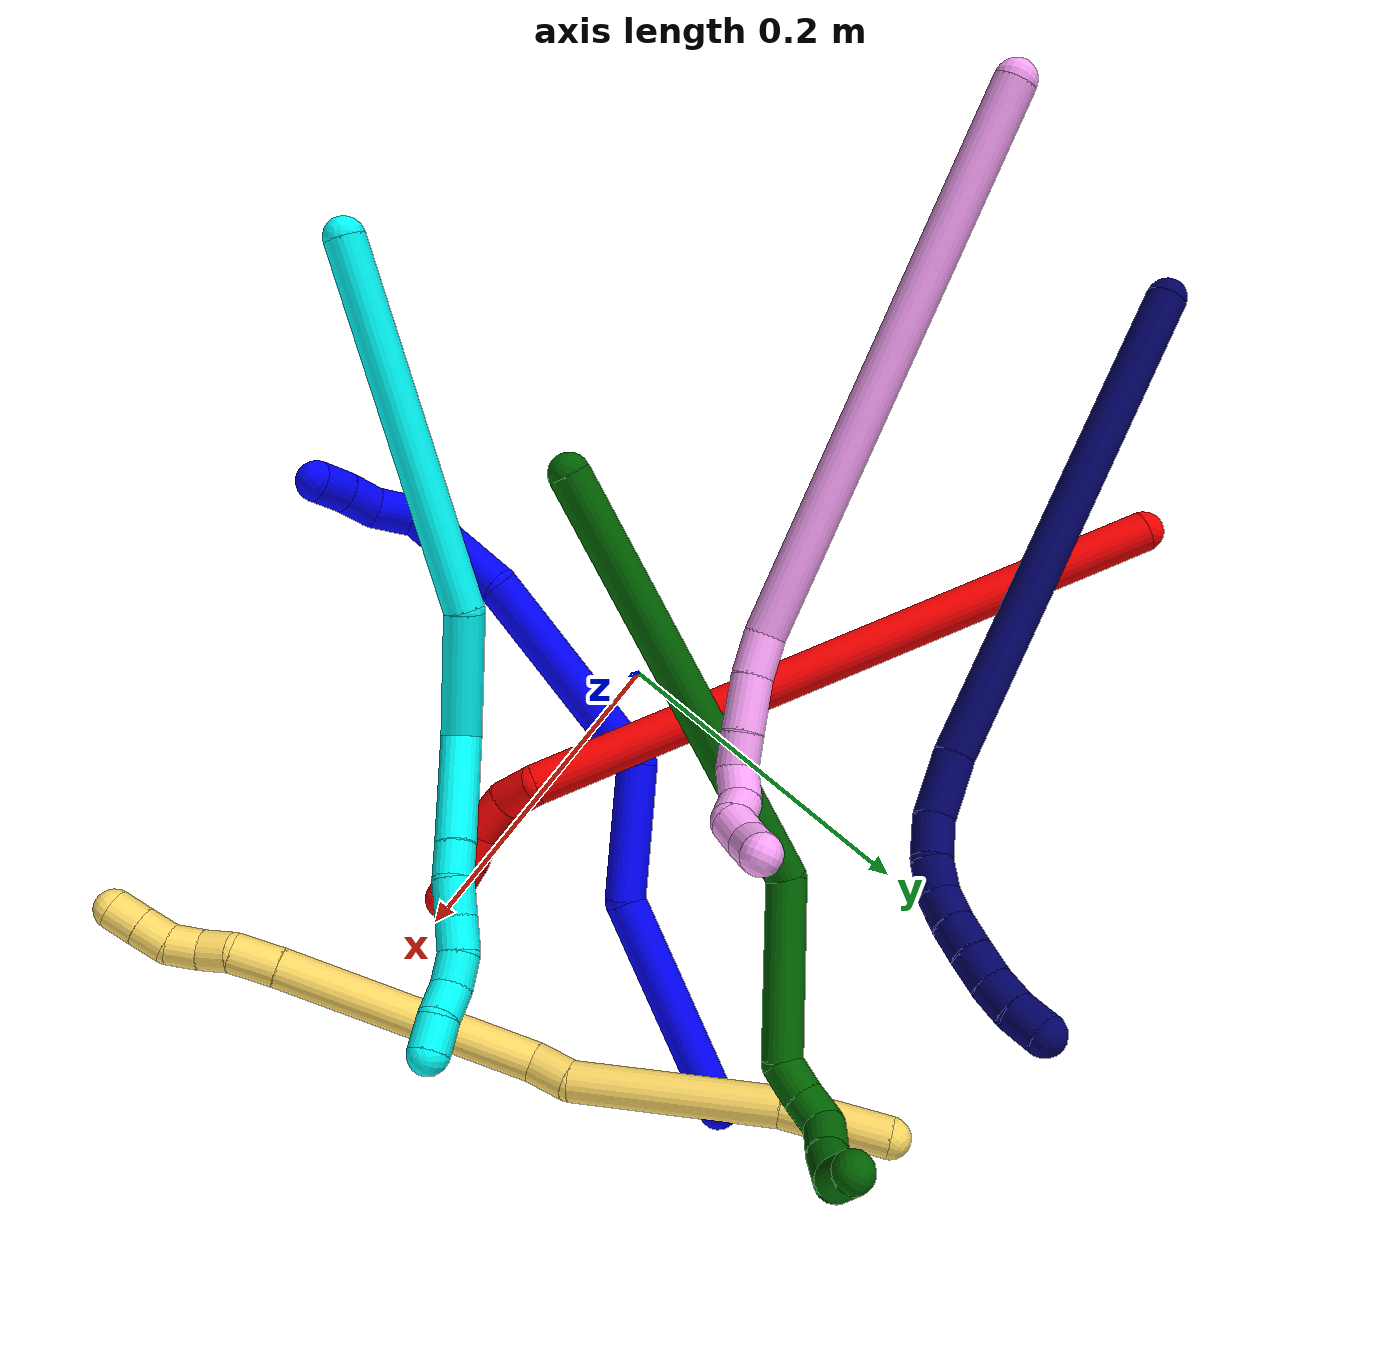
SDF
<sdf version="1.7">
 <world name="default">
  <plugin name="TubeGeneratorPlugin" filename="libtube_generator_plugin.so"/>
  <model name="photoneo_s_sensor">
   <static>1</static>
   <pose>0 0 2 1.57079 1.57079 3.14159</pose>
   <link name="link">
    <inertial><mass>0.1</mass></inertial>
    <sensor name="sensor" type="depth">
     <update_rate>30</update_rate>
     <camera>
      <horizontal_fov>1.22</horizontal_fov>
      <image><width>1920</width><height>1200</height><format>B8G8R8</format></image>
      <clip><near>0.1</near><far>4</far></clip>
      <depth_camera><output>points</output></depth_camera>
     </camera>
     <plugin name="camera_plugin" filename="libgazebo_ros_depth_camera.so">
      <baseline>0.2</baseline>
      <alwaysOn>1</alwaysOn>
      <updateRate>0.0</updateRate>
      <cameraName>camera_ir</cameraName>
      <imageTopicName>/camera/color/image_raw</imageTopicName>
      <cameraInfoTopicName>/camera/color/camera_info</cameraInfoTopicName>
      <depthImageTopicName>/camera/depth/image_raw</depthImageTopicName>
      <depthImageCameraInfoTopicName>/camera/depth/camera_info</depthImageCameraInfoTopicName>
      <pointCloudTopicName>/camera/depth/points</pointCloudTopicName>
      <frameName>fr_optical</frameName>
      <pointCloudCutoff>0.1</pointCloudCutoff>
      <pointCloudCutoffMax>2.0</pointCloudCutoffMax>
      <distortionK1>0</distortionK1>
      <distortionK2>0</distortionK2>
      <distortionK3>0</distortionK3>
      <distortionT1>0</distortionT1>
      <distortionT2>0</distortionT2>
      <CxPrime>0</CxPrime>
      <Cx>0</Cx>
      <Cy>0</Cy>
      <focalLength>0</focalLength>
      <hackBaseline>0</hackBaseline>
     </plugin>
    </sensor>
   </link>
  </model>
  <gravity>0 0 -9.8</gravity>
  <magnetic_field>6e-06 2.3e-05 -4.2e-05</magnetic_field>
  <atmosphere type="adiabatic"/>
  <physics name="default_physics" default="0" type="ode">
   <max_step_size>0.003</max_step_size>
   <real_time_factor>1</real_time_factor>
   <real_time_update_rate>1000</real_time_update_rate>
   <max_contacts>10000</max_contacts>
   <ode>
    <solver>
     <type>quick</type>
     <iters>100</iters>
     <sor>1.3</sor>
     <use_dynamic_moi_rescaling>0</use_dynamic_moi_rescaling>
    </solver>
    <constraints>
     <contact_max_correcting_vel>0</contact_max_correcting_vel>
     <contact_surface_layer>0.001</contact_surface_layer>
     <cfm>0</cfm>
     <erp>0.2</erp>
    </constraints>
   </ode>
  </physics>
  <scene><ambient>0.4 0.4 0.4 1</ambient><background>0.7 0.7 0.7 1</background><shadows>0</shadows></scene>
  <audio><device>default</device></audio>
  <spherical_coordinates>
   <surface_model>EARTH_WGS84</surface_model>
   <latitude_deg>0</latitude_deg>
   <longitude_deg>0</longitude_deg>
   <elevation>0</elevation>
   <heading_deg>0</heading_deg>
  </spherical_coordinates>
  <model name="bin">
   <static>1</static>
   <link name="bottom">
    <collision name="collision-bottom">
     <pose>0 0 -0.01 0 -0 0</pose>
     <geometry><box><size>0.8 0.6 0.02</size></box></geometry>
     <surface>
      <friction><ode><mu>100</mu><mu2>100</mu2></ode></friction>
      <contact><collide_bitmask>65535</collide_bitmask></contact>
     </surface>
    </collision>
   </link>
   <link name="west_wall">
    <collision name="collision-west_wall">
     <pose>-0.41 0 0.1 0 -0 0</pose>
     <geometry><box><size>0.02 0.6 0.2</size></box></geometry>
     <surface>
      <friction><ode><mu>100</mu><mu2>100</mu2></ode></friction>
      <contact><collide_bitmask>65535</collide_bitmask></contact>
     </surface>
    </collision>
   </link>
   <link name="east_wall">
    <collision name="collision-east_wall">
     <pose>0.41 0 0.1 0 -0 0</pose>
     <geometry><box><size>0.02 0.6 0.2</size></box></geometry>
     <surface>
      <friction><ode><mu>100</mu><mu2>100</mu2></ode></friction>
      <contact><collide_bitmask>65535</collide_bitmask></contact>
     </surface>
    </collision>
   </link>
   <link name="south_wall">
    <collision name="collision-south_wall">
     <pose>0 -0.31 0.1 0 -0 0</pose>
     <geometry><box><size>0.8 0.02 0.2</size></box></geometry>
     <surface>
      <friction><ode><mu>100</mu><mu2>100</mu2></ode></friction>
      <contact><collide_bitmask>65535</collide_bitmask></contact>
     </surface>
    </collision>
   </link>
   <link name="north_wall">
    <collision name="collision-north_wall">
     <pose>0 0.31 0.1 0 -0 0</pose>
     <geometry><box><size>0.8 0.02 0.2</size></box></geometry>
     <surface>
      <friction><ode><mu>100</mu><mu2>100</mu2></ode></friction>
      <contact><collide_bitmask>65535</collide_bitmask></contact>
     </surface>
    </collision>
   </link>
  </model>
  <model name="1">
   <static>0</static>
   <link name="1">
    <collision name="collision-cylinder-e_1_1_4">
     <pose>0.021065 -0.063349 -0.022676 1.91453 0.303402 0.427557</pose>
     <geometry><cylinder><radius>0.0125</radius><length>0.141012</length></cylinder></geometry>
     <surface>
      <friction><ode><mu>1.16</mu><mu2>1.16</mu2><slip1>0</slip1><slip2>0</slip2></ode></friction>
      <contact><ode><kp>1e+06</kp><kd>1</kd><max_vel>0</max_vel><min_depth>0.001</min_depth></ode></contact>
     </surface>
    </collision>
    <visual name="visual-cylinder-e_1_1_4">
     <pose>0.021065 -0.063349 -0.022676 1.91453 0.303402 0.427557</pose>
     <geometry><cylinder><radius>0.0125</radius><length>0.141012</length></cylinder></geometry>
     <material><ambient>0 0 1 1</ambient></material>
    </visual>
    <collision name="collision-cylinder-e_2_4_5">
     <pose>0.047433 -0.154496 -0.076341 2.41045 0.126707 0.328478</pose>
     <geometry><cylinder><radius>0.0125</radius><length>0.083933</length></cylinder></geometry>
     <surface>
      <friction><ode><mu>1.16</mu><mu2>1.16</mu2><slip1>0</slip1><slip2>0</slip2></ode></friction>
      <contact><ode><kp>1e+06</kp><kd>1</kd><max_vel>0</max_vel><min_depth>0.001</min_depth></ode></contact>
     </surface>
    </collision>
    <visual name="visual-cylinder-e_2_4_5">
     <pose>0.047433 -0.154496 -0.076341 2.41045 0.126707 0.328478</pose>
     <geometry><cylinder><radius>0.0125</radius><length>0.083933</length></cylinder></geometry>
     <material><ambient>0 0 1 1</ambient></material>
    </visual>
    <collision name="collision-cylinder-e_3_5_6">
     <pose>0.07616 -0.247343 -0.112954 1.65702 0.34445 0.374815</pose>
     <geometry><cylinder><radius>0.0125</radius><length>0.138733</length></cylinder></geometry>
     <surface>
      <friction><ode><mu>1.16</mu><mu2>1.16</mu2><slip1>0</slip1><slip2>0</slip2></ode></friction>
      <contact><ode><kp>1e+06</kp><kd>1</kd><max_vel>0</max_vel><min_depth>0.001</min_depth></ode></contact>
     </surface>
    </collision>
    <visual name="visual-cylinder-e_3_5_6">
     <pose>0.07616 -0.247343 -0.112954 1.65702 0.34445 0.374815</pose>
     <geometry><cylinder><radius>0.0125</radius><length>0.138733</length></cylinder></geometry>
     <material><ambient>0 0 1 1</ambient></material>
    </visual>
    <collision name="collision-cylinder-e_4_6_7">
     <pose>0.121685 -0.338419 -0.118002 1.54873 0.70389 0.689727</pose>
     <geometry><cylinder><radius>0.0125</radius><length>0.0683</length></cylinder></geometry>
     <surface>
      <friction><ode><mu>1.16</mu><mu2>1.16</mu2><slip1>0</slip1><slip2>0</slip2></ode></friction>
      <contact><ode><kp>1e+06</kp><kd>1</kd><max_vel>0</max_vel><min_depth>0.001</min_depth></ode></contact>
     </surface>
    </collision>
    <visual name="visual-cylinder-e_4_6_7">
     <pose>0.121685 -0.338419 -0.118002 1.54873 0.70389 0.689727</pose>
     <geometry><cylinder><radius>0.0125</radius><length>0.0683</length></cylinder></geometry>
     <material><ambient>0 0 1 1</ambient></material>
    </visual>
    <collision name="collision-cylinder-e_5_7_8">
     <pose>0.146867 -0.374519 -0.109237 0.888066 0.232974 0.111219</pose>
     <geometry><cylinder><radius>0.0125</radius><length>0.026686</length></cylinder></geometry>
     <surface>
      <friction><ode><mu>1.16</mu><mu2>1.16</mu2><slip1>0</slip1><slip2>0</slip2></ode></friction>
      <contact><ode><kp>1e+06</kp><kd>1</kd><max_vel>0</max_vel><min_depth>0.001</min_depth></ode></contact>
     </surface>
    </collision>
    <visual name="visual-cylinder-e_5_7_8">
     <pose>0.146867 -0.374519 -0.109237 0.888066 0.232974 0.111219</pose>
     <geometry><cylinder><radius>0.0125</radius><length>0.026686</length></cylinder></geometry>
     <material><ambient>0 0 1 1</ambient></material>
    </visual>
    <collision name="collision-cylinder-e_6_8_9">
     <pose>0.149223 -0.39402 -0.096605 1.13059 -0.069378 -0.044021</pose>
     <geometry><cylinder><radius>0.0125</radius><length>0.020894</length></cylinder></geometry>
     <surface>
      <friction><ode><mu>1.16</mu><mu2>1.16</mu2><slip1>0</slip1><slip2>0</slip2></ode></friction>
      <contact><ode><kp>1e+06</kp><kd>1</kd><max_vel>0</max_vel><min_depth>0.001</min_depth></ode></contact>
     </surface>
    </collision>
    <visual name="visual-cylinder-e_6_8_9">
     <pose>0.149223 -0.39402 -0.096605 1.13059 -0.069378 -0.044021</pose>
     <geometry><cylinder><radius>0.0125</radius><length>0.020894</length></cylinder></geometry>
     <material><ambient>0 0 1 1</ambient></material>
    </visual>
    <collision name="collision-cylinder-e_7_9_2">
     <pose>0.146779 -0.411952 -0.08676 1.00467 -0.169099 -0.093048</pose>
     <geometry><cylinder><radius>0.0125</radius><length>0.020443</length></cylinder></geometry>
     <surface>
      <friction><ode><mu>1.16</mu><mu2>1.16</mu2><slip1>0</slip1><slip2>0</slip2></ode></friction>
      <contact><ode><kp>1e+06</kp><kd>1</kd><max_vel>0</max_vel><min_depth>0.001</min_depth></ode></contact>
     </surface>
    </collision>
    <visual name="visual-cylinder-e_7_9_2">
     <pose>0.146779 -0.411952 -0.08676 1.00467 -0.169099 -0.093048</pose>
     <geometry><cylinder><radius>0.0125</radius><length>0.020443</length></cylinder></geometry>
     <material><ambient>0 0 1 1</ambient></material>
    </visual>
    <collision name="collision-sphere-2">
     <pose>0.145059 -0.420455 -0.081356 0 -0 0</pose>
     <geometry><sphere><radius>0.0125</radius></sphere></geometry>
     <surface>
      <friction><ode><mu>1.16</mu><mu2>1.16</mu2><slip1>0</slip1><slip2>0</slip2></ode></friction>
      <contact><ode><kp>1e+06</kp><kd>1</kd><max_vel>0</max_vel><min_depth>0.001</min_depth></ode></contact>
     </surface>
    </collision>
    <visual name="visual-sphere-2">
     <pose>0.145059 -0.420455 -0.081356 0 -0 0</pose>
     <geometry><sphere><radius>0.0125</radius></sphere></geometry>
     <material><ambient>0 0 1 1</ambient></material>
    </visual>
    <collision name="collision-sphere-9">
     <pose>0.148499 -0.403448 -0.092164 0 -0 0</pose>
     <geometry><sphere><radius>0.0125</radius></sphere></geometry>
     <surface>
      <friction><ode><mu>1.16</mu><mu2>1.16</mu2><slip1>0</slip1><slip2>0</slip2></ode></friction>
      <contact><ode><kp>1e+06</kp><kd>1</kd><max_vel>0</max_vel><min_depth>0.001</min_depth></ode></contact>
     </surface>
    </collision>
    <visual name="visual-sphere-9">
     <pose>0.148499 -0.403448 -0.092164 0 -0 0</pose>
     <geometry><sphere><radius>0.0125</radius></sphere></geometry>
     <material><ambient>0 0 1 1</ambient></material>
    </visual>
    <collision name="collision-sphere-4">
     <pose>0.04213 -0.126699 -0.045352 0 -0 0</pose>
     <geometry><sphere><radius>0.0125</radius></sphere></geometry>
     <surface>
      <friction><ode><mu>1.16</mu><mu2>1.16</mu2><slip1>0</slip1><slip2>0</slip2></ode></friction>
      <contact><ode><kp>1e+06</kp><kd>1</kd><max_vel>0</max_vel><min_depth>0.001</min_depth></ode></contact>
     </surface>
    </collision>
    <visual name="visual-sphere-4">
     <pose>0.04213 -0.126699 -0.045352 0 -0 0</pose>
     <geometry><sphere><radius>0.0125</radius></sphere></geometry>
     <material><ambient>0 0 1 1</ambient></material>
    </visual>
    <collision name="collision-sphere-1">
     <geometry><sphere><radius>0.0125</radius></sphere></geometry>
     <surface>
      <friction><ode><mu>1.16</mu><mu2>1.16</mu2><slip1>0</slip1><slip2>0</slip2></ode></friction>
      <contact><ode><kp>1e+06</kp><kd>1</kd><max_vel>0</max_vel><min_depth>0.001</min_depth></ode></contact>
     </surface>
    </collision>
    <visual name="visual-sphere-1">
     <geometry><sphere><radius>0.0125</radius></sphere></geometry>
     <material><ambient>0 0 1 1</ambient></material>
    </visual>
    <collision name="collision-sphere-8">
     <pose>0.149947 -0.384591 -0.101046 0 -0 0</pose>
     <geometry><sphere><radius>0.0125</radius></sphere></geometry>
     <surface>
      <friction><ode><mu>1.16</mu><mu2>1.16</mu2><slip1>0</slip1><slip2>0</slip2></ode></friction>
      <contact><ode><kp>1e+06</kp><kd>1</kd><max_vel>0</max_vel><min_depth>0.001</min_depth></ode></contact>
     </surface>
    </collision>
    <visual name="visual-sphere-8">
     <pose>0.149947 -0.384591 -0.101046 0 -0 0</pose>
     <geometry><sphere><radius>0.0125</radius></sphere></geometry>
     <material><ambient>0 0 1 1</ambient></material>
    </visual>
    <collision name="collision-sphere-5">
     <pose>0.052736 -0.182293 -0.107331 0 -0 0</pose>
     <geometry><sphere><radius>0.0125</radius></sphere></geometry>
     <surface>
      <friction><ode><mu>1.16</mu><mu2>1.16</mu2><slip1>0</slip1><slip2>0</slip2></ode></friction>
      <contact><ode><kp>1e+06</kp><kd>1</kd><max_vel>0</max_vel><min_depth>0.001</min_depth></ode></contact>
     </surface>
    </collision>
    <visual name="visual-sphere-5">
     <pose>0.052736 -0.182293 -0.107331 0 -0 0</pose>
     <geometry><sphere><radius>0.0125</radius></sphere></geometry>
     <material><ambient>0 0 1 1</ambient></material>
    </visual>
    <collision name="collision-sphere-6">
     <pose>0.099584 -0.312392 -0.118577 0 -0 0</pose>
     <geometry><sphere><radius>0.0125</radius></sphere></geometry>
     <surface>
      <friction><ode><mu>1.16</mu><mu2>1.16</mu2><slip1>0</slip1><slip2>0</slip2></ode></friction>
      <contact><ode><kp>1e+06</kp><kd>1</kd><max_vel>0</max_vel><min_depth>0.001</min_depth></ode></contact>
     </surface>
    </collision>
    <visual name="visual-sphere-6">
     <pose>0.099584 -0.312392 -0.118577 0 -0 0</pose>
     <geometry><sphere><radius>0.0125</radius></sphere></geometry>
     <material><ambient>0 0 1 1</ambient></material>
    </visual>
    <collision name="collision-sphere-7">
     <pose>0.143786 -0.364446 -0.117428 0 -0 0</pose>
     <geometry><sphere><radius>0.0125</radius></sphere></geometry>
     <surface>
      <friction><ode><mu>1.16</mu><mu2>1.16</mu2><slip1>0</slip1><slip2>0</slip2></ode></friction>
      <contact><ode><kp>1e+06</kp><kd>1</kd><max_vel>0</max_vel><min_depth>0.001</min_depth></ode></contact>
     </surface>
    </collision>
    <visual name="visual-sphere-7">
     <pose>0.143786 -0.364446 -0.117428 0 -0 0</pose>
     <geometry><sphere><radius>0.0125</radius></sphere></geometry>
     <material><ambient>0 0 1 1</ambient></material>
    </visual>
    <inertial>
     <pose>0.071733 -0.211955 -0.080085 0 -0 0</pose>
     <mass>0.5</mass>
     <inertia>
      <ixx>0.000695</ixx>
      <ixy>0</ixy>
      <ixz>0</ixz>
      <iyy>0.000116</iyy>
      <iyz>0</iyz>
      <izz>0.00031</izz>
     </inertia>
    </inertial>
   </link>
   <pose>0.177005 0.207733 0.012493 -0.905794 0.980997 -1.10015</pose>
  </model>
  <model name="2">
   <static>0</static>
   <link name="2">
    <collision name="collision-cylinder-e_1_1_4">
     <pose>0.112132 -0.048036 -0.159849 2.84967 0.591555 2.2426</pose>
     <geometry><cylinder><radius>0.0125</radius><length>0.402158</length></cylinder></geometry>
     <surface>
      <friction><ode><mu>1.16</mu><mu2>1.16</mu2><slip1>0</slip1><slip2>0</slip2></ode></friction>
      <contact><ode><kp>1e+06</kp><kd>1</kd><max_vel>0</max_vel><min_depth>0.001</min_depth></ode></contact>
     </surface>
    </collision>
    <visual name="visual-cylinder-e_1_1_4">
     <pose>0.112132 -0.048036 -0.159849 2.84967 0.591555 2.2426</pose>
     <geometry><cylinder><radius>0.0125</radius><length>0.402158</length></cylinder></geometry>
     <material><ambient>1 0 0 1</ambient></material>
    </visual>
    <collision name="collision-cylinder-e_2_4_5">
     <pose>0.235322 -0.095014 -0.325369 -2.95723 1.08996 -2.83895</pose>
     <geometry><cylinder><radius>0.0125</radius><length>0.024943</length></cylinder></geometry>
     <surface>
      <friction><ode><mu>1.16</mu><mu2>1.16</mu2><slip1>0</slip1><slip2>0</slip2></ode></friction>
      <contact><ode><kp>1e+06</kp><kd>1</kd><max_vel>0</max_vel><min_depth>0.001</min_depth></ode></contact>
     </surface>
    </collision>
    <visual name="visual-cylinder-e_2_4_5">
     <pose>0.235322 -0.095014 -0.325369 -2.95723 1.08996 -2.83895</pose>
     <geometry><cylinder><radius>0.0125</radius><length>0.024943</length></cylinder></geometry>
     <material><ambient>1 0 0 1</ambient></material>
    </visual>
    <collision name="collision-cylinder-e_3_5_6">
     <pose>0.25782 -0.098333 -0.335589 2.37562 1.06654 1.94385</pose>
     <geometry><cylinder><radius>0.0125</radius><length>0.026133</length></cylinder></geometry>
     <surface>
      <friction><ode><mu>1.16</mu><mu2>1.16</mu2><slip1>0</slip1><slip2>0</slip2></ode></friction>
      <contact><ode><kp>1e+06</kp><kd>1</kd><max_vel>0</max_vel><min_depth>0.001</min_depth></ode></contact>
     </surface>
    </collision>
    <visual name="visual-cylinder-e_3_5_6">
     <pose>0.25782 -0.098333 -0.335589 2.37562 1.06654 1.94385</pose>
     <geometry><cylinder><radius>0.0125</radius><length>0.026133</length></cylinder></geometry>
     <material><ambient>1 0 0 1</ambient></material>
    </visual>
    <collision name="collision-cylinder-e_4_6_7">
     <pose>0.277716 -0.108188 -0.341156 1.75436 0.988204 1.14976</pose>
     <geometry><cylinder><radius>0.0125</radius><length>0.020253</length></cylinder></geometry>
     <surface>
      <friction><ode><mu>1.16</mu><mu2>1.16</mu2><slip1>0</slip1><slip2>0</slip2></ode></friction>
      <contact><ode><kp>1e+06</kp><kd>1</kd><max_vel>0</max_vel><min_depth>0.001</min_depth></ode></contact>
     </surface>
    </collision>
    <visual name="visual-cylinder-e_4_6_7">
     <pose>0.277716 -0.108188 -0.341156 1.75436 0.988204 1.14976</pose>
     <geometry><cylinder><radius>0.0125</radius><length>0.020253</length></cylinder></geometry>
     <material><ambient>1 0 0 1</ambient></material>
    </visual>
    <collision name="collision-cylinder-e_5_7_2">
     <pose>0.295705 -0.121771 -0.346548 2.06573 0.802582 1.2364</pose>
     <geometry><cylinder><radius>0.0125</radius><length>0.026512</length></cylinder></geometry>
     <surface>
      <friction><ode><mu>1.16</mu><mu2>1.16</mu2><slip1>0</slip1><slip2>0</slip2></ode></friction>
      <contact><ode><kp>1e+06</kp><kd>1</kd><max_vel>0</max_vel><min_depth>0.001</min_depth></ode></contact>
     </surface>
    </collision>
    <visual name="visual-cylinder-e_5_7_2">
     <pose>0.295705 -0.121771 -0.346548 2.06573 0.802582 1.2364</pose>
     <geometry><cylinder><radius>0.0125</radius><length>0.026512</length></cylinder></geometry>
     <material><ambient>1 0 0 1</ambient></material>
    </visual>
    <collision name="collision-sphere-2">
     <pose>0.305239 -0.129877 -0.350923 0 -0 0</pose>
     <geometry><sphere><radius>0.0125</radius></sphere></geometry>
     <surface>
      <friction><ode><mu>1.16</mu><mu2>1.16</mu2><slip1>0</slip1><slip2>0</slip2></ode></friction>
      <contact><ode><kp>1e+06</kp><kd>1</kd><max_vel>0</max_vel><min_depth>0.001</min_depth></ode></contact>
     </surface>
    </collision>
    <visual name="visual-sphere-2">
     <pose>0.305239 -0.129877 -0.350923 0 -0 0</pose>
     <geometry><sphere><radius>0.0125</radius></sphere></geometry>
     <material><ambient>1 0 0 1</ambient></material>
    </visual>
    <collision name="collision-sphere-7">
     <pose>0.286172 -0.113666 -0.342173 0 -0 0</pose>
     <geometry><sphere><radius>0.0125</radius></sphere></geometry>
     <surface>
      <friction><ode><mu>1.16</mu><mu2>1.16</mu2><slip1>0</slip1><slip2>0</slip2></ode></friction>
      <contact><ode><kp>1e+06</kp><kd>1</kd><max_vel>0</max_vel><min_depth>0.001</min_depth></ode></contact>
     </surface>
    </collision>
    <visual name="visual-sphere-7">
     <pose>0.286172 -0.113666 -0.342173 0 -0 0</pose>
     <geometry><sphere><radius>0.0125</radius></sphere></geometry>
     <material><ambient>1 0 0 1</ambient></material>
    </visual>
    <collision name="collision-sphere-6">
     <pose>0.26926 -0.10271 -0.340139 0 -0 0</pose>
     <geometry><sphere><radius>0.0125</radius></sphere></geometry>
     <surface>
      <friction><ode><mu>1.16</mu><mu2>1.16</mu2><slip1>0</slip1><slip2>0</slip2></ode></friction>
      <contact><ode><kp>1e+06</kp><kd>1</kd><max_vel>0</max_vel><min_depth>0.001</min_depth></ode></contact>
     </surface>
    </collision>
    <visual name="visual-sphere-6">
     <pose>0.26926 -0.10271 -0.340139 0 -0 0</pose>
     <geometry><sphere><radius>0.0125</radius></sphere></geometry>
     <material><ambient>1 0 0 1</ambient></material>
    </visual>
    <collision name="collision-sphere-5">
     <pose>0.246379 -0.093956 -0.331039 0 -0 0</pose>
     <geometry><sphere><radius>0.0125</radius></sphere></geometry>
     <surface>
      <friction><ode><mu>1.16</mu><mu2>1.16</mu2><slip1>0</slip1><slip2>0</slip2></ode></friction>
      <contact><ode><kp>1e+06</kp><kd>1</kd><max_vel>0</max_vel><min_depth>0.001</min_depth></ode></contact>
     </surface>
    </collision>
    <visual name="visual-sphere-5">
     <pose>0.246379 -0.093956 -0.331039 0 -0 0</pose>
     <geometry><sphere><radius>0.0125</radius></sphere></geometry>
     <material><ambient>1 0 0 1</ambient></material>
    </visual>
    <collision name="collision-sphere-1">
     <geometry><sphere><radius>0.0125</radius></sphere></geometry>
     <surface>
      <friction><ode><mu>1.16</mu><mu2>1.16</mu2><slip1>0</slip1><slip2>0</slip2></ode></friction>
      <contact><ode><kp>1e+06</kp><kd>1</kd><max_vel>0</max_vel><min_depth>0.001</min_depth></ode></contact>
     </surface>
    </collision>
    <visual name="visual-sphere-1">
     <geometry><sphere><radius>0.0125</radius></sphere></geometry>
     <material><ambient>1 0 0 1</ambient></material>
    </visual>
    <collision name="collision-sphere-4">
     <pose>0.224265 -0.096071 -0.319698 0 -0 0</pose>
     <geometry><sphere><radius>0.0125</radius></sphere></geometry>
     <surface>
      <friction><ode><mu>1.16</mu><mu2>1.16</mu2><slip1>0</slip1><slip2>0</slip2></ode></friction>
      <contact><ode><kp>1e+06</kp><kd>1</kd><max_vel>0</max_vel><min_depth>0.001</min_depth></ode></contact>
     </surface>
    </collision>
    <visual name="visual-sphere-4">
     <pose>0.224265 -0.096071 -0.319698 0 -0 0</pose>
     <geometry><sphere><radius>0.0125</radius></sphere></geometry>
     <material><ambient>1 0 0 1</ambient></material>
    </visual>
    <inertial>
     <pose>0.142333 -0.059354 -0.194535 0 -0 0</pose>
     <mass>0.5</mass>
     <inertia>
      <ixx>0.00075</ixx>
      <ixy>0</ixy>
      <ixz>0</ixz>
      <iyy>0.007454</iyy>
      <iyz>0</iyz>
      <izz>-0.001764</izz>
     </inertia>
    </inertial>
   </link>
   <pose>-0.263123 0.186565 0.012518 -2.04991 0.715386 0.14252</pose>
  </model>
  <model name="3">
   <static>0</static>
   <link name="3">
    <collision name="collision-cylinder-e_1_1_4">
     <pose>0.067371 0.082291 0.037738 -1.14082 0.639765 -0.418807</pose>
     <geometry><cylinder><radius>0.0125</radius><length>0.225697</length></cylinder></geometry>
     <surface>
      <friction><ode><mu>1.16</mu><mu2>1.16</mu2><slip1>0</slip1><slip2>0</slip2></ode></friction>
      <contact><ode><kp>1e+06</kp><kd>1</kd><max_vel>0</max_vel><min_depth>0.001</min_depth></ode></contact>
     </surface>
    </collision>
    <visual name="visual-cylinder-e_1_1_4">
     <pose>0.067371 0.082291 0.037738 -1.14082 0.639765 -0.418807</pose>
     <geometry><cylinder><radius>0.0125</radius><length>0.225697</length></cylinder></geometry>
     <material><ambient>0.003922 1 0.996078 1</ambient></material>
    </visual>
    <collision name="collision-cylinder-e_2_4_5">
     <pose>0.146873 0.200974 0.084964 -1.31574 0.311994 -0.241865</pose>
     <geometry><cylinder><radius>0.0125</radius><length>0.079034</length></cylinder></geometry>
     <surface>
      <friction><ode><mu>1.16</mu><mu2>1.16</mu2><slip1>0</slip1><slip2>0</slip2></ode></friction>
      <contact><ode><kp>1e+06</kp><kd>1</kd><max_vel>0</max_vel><min_depth>0.001</min_depth></ode></contact>
     </surface>
    </collision>
    <visual name="visual-cylinder-e_2_4_5">
     <pose>0.146873 0.200974 0.084964 -1.31574 0.311994 -0.241865</pose>
     <geometry><cylinder><radius>0.0125</radius><length>0.079034</length></cylinder></geometry>
     <material><ambient>0.003922 1 0.996078 1</ambient></material>
    </visual>
    <collision name="collision-cylinder-e_3_5_6">
     <pose>0.182584 0.260476 0.082961 -2.03227 0.740316 -1.11914</pose>
     <geometry><cylinder><radius>0.0125</radius><length>0.06992</length></cylinder></geometry>
     <surface>
      <friction><ode><mu>1.16</mu><mu2>1.16</mu2><slip1>0</slip1><slip2>0</slip2></ode></friction>
      <contact><ode><kp>1e+06</kp><kd>1</kd><max_vel>0</max_vel><min_depth>0.001</min_depth></ode></contact>
     </surface>
    </collision>
    <visual name="visual-cylinder-e_3_5_6">
     <pose>0.182584 0.260476 0.082961 -2.03227 0.740316 -1.11914</pose>
     <geometry><cylinder><radius>0.0125</radius><length>0.06992</length></cylinder></geometry>
     <material><ambient>0.003922 1 0.996078 1</ambient></material>
    </visual>
    <collision name="collision-cylinder-e_4_6_7">
     <pose>0.212851 0.290991 0.068357 -1.96865 0.694155 -0.997043</pose>
     <geometry><cylinder><radius>0.0125</radius><length>0.020901</length></cylinder></geometry>
     <surface>
      <friction><ode><mu>1.16</mu><mu2>1.16</mu2><slip1>0</slip1><slip2>0</slip2></ode></friction>
      <contact><ode><kp>1e+06</kp><kd>1</kd><max_vel>0</max_vel><min_depth>0.001</min_depth></ode></contact>
     </surface>
    </collision>
    <visual name="visual-cylinder-e_4_6_7">
     <pose>0.212851 0.290991 0.068357 -1.96865 0.694155 -0.997043</pose>
     <geometry><cylinder><radius>0.0125</radius><length>0.020901</length></cylinder></geometry>
     <material><ambient>0.003922 1 0.996078 1</ambient></material>
    </visual>
    <collision name="collision-cylinder-e_5_7_8">
     <pose>0.227687 0.306579 0.063714 -1.75573 0.774762 -0.913487</pose>
     <geometry><cylinder><radius>0.0125</radius><length>0.023301</length></cylinder></geometry>
     <surface>
      <friction><ode><mu>1.16</mu><mu2>1.16</mu2><slip1>0</slip1><slip2>0</slip2></ode></friction>
      <contact><ode><kp>1e+06</kp><kd>1</kd><max_vel>0</max_vel><min_depth>0.001</min_depth></ode></contact>
     </surface>
    </collision>
    <visual name="visual-cylinder-e_5_7_8">
     <pose>0.227687 0.306579 0.063714 -1.75573 0.774762 -0.913487</pose>
     <geometry><cylinder><radius>0.0125</radius><length>0.023301</length></cylinder></geometry>
     <material><ambient>0.003922 1 0.996078 1</ambient></material>
    </visual>
    <collision name="collision-cylinder-e_6_8_9">
     <pose>0.243308 0.321573 0.060257 -1.84633 0.812417 -1.03402</pose>
     <geometry><cylinder><radius>0.0125</radius><length>0.020582</length></cylinder></geometry>
     <surface>
      <friction><ode><mu>1.16</mu><mu2>1.16</mu2><slip1>0</slip1><slip2>0</slip2></ode></friction>
      <contact><ode><kp>1e+06</kp><kd>1</kd><max_vel>0</max_vel><min_depth>0.001</min_depth></ode></contact>
     </surface>
    </collision>
    <visual name="visual-cylinder-e_6_8_9">
     <pose>0.243308 0.321573 0.060257 -1.84633 0.812417 -1.03402</pose>
     <geometry><cylinder><radius>0.0125</radius><length>0.020582</length></cylinder></geometry>
     <material><ambient>0.003922 1 0.996078 1</ambient></material>
    </visual>
    <collision name="collision-cylinder-e_7_9_10">
     <pose>0.255952 0.33618 0.054679 -2.00893 0.541122 -0.8227</pose>
     <geometry><cylinder><radius>0.0125</radius><length>0.020089</length></cylinder></geometry>
     <surface>
      <friction><ode><mu>1.16</mu><mu2>1.16</mu2><slip1>0</slip1><slip2>0</slip2></ode></friction>
      <contact><ode><kp>1e+06</kp><kd>1</kd><max_vel>0</max_vel><min_depth>0.001</min_depth></ode></contact>
     </surface>
    </collision>
    <visual name="visual-cylinder-e_7_9_10">
     <pose>0.255952 0.33618 0.054679 -2.00893 0.541122 -0.8227</pose>
     <geometry><cylinder><radius>0.0125</radius><length>0.020089</length></cylinder></geometry>
     <material><ambient>0.003922 1 0.996078 1</ambient></material>
    </visual>
    <collision name="collision-cylinder-e_8_10_11">
     <pose>0.26605 0.349713 0.044364 -2.43073 0.510496 -1.22544</pose>
     <geometry><cylinder><radius>0.0125</radius><length>0.020152</length></cylinder></geometry>
     <surface>
      <friction><ode><mu>1.16</mu><mu2>1.16</mu2><slip1>0</slip1><slip2>0</slip2></ode></friction>
      <contact><ode><kp>1e+06</kp><kd>1</kd><max_vel>0</max_vel><min_depth>0.001</min_depth></ode></contact>
     </surface>
    </collision>
    <visual name="visual-cylinder-e_8_10_11">
     <pose>0.26605 0.349713 0.044364 -2.43073 0.510496 -1.22544</pose>
     <geometry><cylinder><radius>0.0125</radius><length>0.020152</length></cylinder></geometry>
     <material><ambient>0.003922 1 0.996078 1</ambient></material>
    </visual>
    <collision name="collision-cylinder-e_9_11_2">
     <pose>0.276059 0.362997 0.033183 -2.1103 0.524225 -0.884177</pose>
     <geometry><cylinder><radius>0.0125</radius><length>0.020323</length></cylinder></geometry>
     <surface>
      <friction><ode><mu>1.16</mu><mu2>1.16</mu2><slip1>0</slip1><slip2>0</slip2></ode></friction>
      <contact><ode><kp>1e+06</kp><kd>1</kd><max_vel>0</max_vel><min_depth>0.001</min_depth></ode></contact>
     </surface>
    </collision>
    <visual name="visual-cylinder-e_9_11_2">
     <pose>0.276059 0.362997 0.033183 -2.1103 0.524225 -0.884177</pose>
     <geometry><cylinder><radius>0.0125</radius><length>0.020323</length></cylinder></geometry>
     <material><ambient>0.003922 1 0.996078 1</ambient></material>
    </visual>
    <collision name="collision-sphere-2">
     <pose>0.281145 0.370544 0.028664 0 -0 0</pose>
     <geometry><sphere><radius>0.0125</radius></sphere></geometry>
     <surface>
      <friction><ode><mu>1.16</mu><mu2>1.16</mu2><slip1>0</slip1><slip2>0</slip2></ode></friction>
      <contact><ode><kp>1e+06</kp><kd>1</kd><max_vel>0</max_vel><min_depth>0.001</min_depth></ode></contact>
     </surface>
    </collision>
    <visual name="visual-sphere-2">
     <pose>0.281145 0.370544 0.028664 0 -0 0</pose>
     <geometry><sphere><radius>0.0125</radius></sphere></geometry>
     <material><ambient>0.003922 1 0.996078 1</ambient></material>
    </visual>
    <collision name="collision-sphere-11">
     <pose>0.270973 0.355449 0.037702 0 -0 0</pose>
     <geometry><sphere><radius>0.0125</radius></sphere></geometry>
     <surface>
      <friction><ode><mu>1.16</mu><mu2>1.16</mu2><slip1>0</slip1><slip2>0</slip2></ode></friction>
      <contact><ode><kp>1e+06</kp><kd>1</kd><max_vel>0</max_vel><min_depth>0.001</min_depth></ode></contact>
     </surface>
    </collision>
    <visual name="visual-sphere-11">
     <pose>0.270973 0.355449 0.037702 0 -0 0</pose>
     <geometry><sphere><radius>0.0125</radius></sphere></geometry>
     <material><ambient>0.003922 1 0.996078 1</ambient></material>
    </visual>
    <collision name="collision-sphere-10">
     <pose>0.261126 0.343977 0.051026 0 -0 0</pose>
     <geometry><sphere><radius>0.0125</radius></sphere></geometry>
     <surface>
      <friction><ode><mu>1.16</mu><mu2>1.16</mu2><slip1>0</slip1><slip2>0</slip2></ode></friction>
      <contact><ode><kp>1e+06</kp><kd>1</kd><max_vel>0</max_vel><min_depth>0.001</min_depth></ode></contact>
     </surface>
    </collision>
    <visual name="visual-sphere-10">
     <pose>0.261126 0.343977 0.051026 0 -0 0</pose>
     <geometry><sphere><radius>0.0125</radius></sphere></geometry>
     <material><ambient>0.003922 1 0.996078 1</ambient></material>
    </visual>
    <collision name="collision-sphere-9">
     <pose>0.250778 0.328384 0.058332 0 -0 0</pose>
     <geometry><sphere><radius>0.0125</radius></sphere></geometry>
     <surface>
      <friction><ode><mu>1.16</mu><mu2>1.16</mu2><slip1>0</slip1><slip2>0</slip2></ode></friction>
      <contact><ode><kp>1e+06</kp><kd>1</kd><max_vel>0</max_vel><min_depth>0.001</min_depth></ode></contact>
     </surface>
    </collision>
    <visual name="visual-sphere-9">
     <pose>0.250778 0.328384 0.058332 0 -0 0</pose>
     <geometry><sphere><radius>0.0125</radius></sphere></geometry>
     <material><ambient>0.003922 1 0.996078 1</ambient></material>
    </visual>
    <collision name="collision-sphere-4">
     <pose>0.134743 0.164581 0.075475 0 -0 0</pose>
     <geometry><sphere><radius>0.0125</radius></sphere></geometry>
     <surface>
      <friction><ode><mu>1.16</mu><mu2>1.16</mu2><slip1>0</slip1><slip2>0</slip2></ode></friction>
      <contact><ode><kp>1e+06</kp><kd>1</kd><max_vel>0</max_vel><min_depth>0.001</min_depth></ode></contact>
     </surface>
    </collision>
    <visual name="visual-sphere-4">
     <pose>0.134743 0.164581 0.075475 0 -0 0</pose>
     <geometry><sphere><radius>0.0125</radius></sphere></geometry>
     <material><ambient>0.003922 1 0.996078 1</ambient></material>
    </visual>
    <collision name="collision-sphere-1">
     <geometry><sphere><radius>0.0125</radius></sphere></geometry>
     <surface>
      <friction><ode><mu>1.16</mu><mu2>1.16</mu2><slip1>0</slip1><slip2>0</slip2></ode></friction>
      <contact><ode><kp>1e+06</kp><kd>1</kd><max_vel>0</max_vel><min_depth>0.001</min_depth></ode></contact>
     </surface>
    </collision>
    <visual name="visual-sphere-1">
     <geometry><sphere><radius>0.0125</radius></sphere></geometry>
     <material><ambient>0.003922 1 0.996078 1</ambient></material>
    </visual>
    <collision name="collision-sphere-8">
     <pose>0.235837 0.314762 0.062183 0 -0 0</pose>
     <geometry><sphere><radius>0.0125</radius></sphere></geometry>
     <surface>
      <friction><ode><mu>1.16</mu><mu2>1.16</mu2><slip1>0</slip1><slip2>0</slip2></ode></friction>
      <contact><ode><kp>1e+06</kp><kd>1</kd><max_vel>0</max_vel><min_depth>0.001</min_depth></ode></contact>
     </surface>
    </collision>
    <visual name="visual-sphere-8">
     <pose>0.235837 0.314762 0.062183 0 -0 0</pose>
     <geometry><sphere><radius>0.0125</radius></sphere></geometry>
     <material><ambient>0.003922 1 0.996078 1</ambient></material>
    </visual>
    <collision name="collision-sphere-5">
     <pose>0.159003 0.237366 0.094453 0 -0 0</pose>
     <geometry><sphere><radius>0.0125</radius></sphere></geometry>
     <surface>
      <friction><ode><mu>1.16</mu><mu2>1.16</mu2><slip1>0</slip1><slip2>0</slip2></ode></friction>
      <contact><ode><kp>1e+06</kp><kd>1</kd><max_vel>0</max_vel><min_depth>0.001</min_depth></ode></contact>
     </surface>
    </collision>
    <visual name="visual-sphere-5">
     <pose>0.159003 0.237366 0.094453 0 -0 0</pose>
     <geometry><sphere><radius>0.0125</radius></sphere></geometry>
     <material><ambient>0.003922 1 0.996078 1</ambient></material>
    </visual>
    <collision name="collision-sphere-6">
     <pose>0.206165 0.283586 0.071469 0 -0 0</pose>
     <geometry><sphere><radius>0.0125</radius></sphere></geometry>
     <surface>
      <friction><ode><mu>1.16</mu><mu2>1.16</mu2><slip1>0</slip1><slip2>0</slip2></ode></friction>
      <contact><ode><kp>1e+06</kp><kd>1</kd><max_vel>0</max_vel><min_depth>0.001</min_depth></ode></contact>
     </surface>
    </collision>
    <visual name="visual-sphere-6">
     <pose>0.206165 0.283586 0.071469 0 -0 0</pose>
     <geometry><sphere><radius>0.0125</radius></sphere></geometry>
     <material><ambient>0.003922 1 0.996078 1</ambient></material>
    </visual>
    <collision name="collision-sphere-7">
     <pose>0.219537 0.298396 0.065244 0 -0 0</pose>
     <geometry><sphere><radius>0.0125</radius></sphere></geometry>
     <surface>
      <friction><ode><mu>1.16</mu><mu2>1.16</mu2><slip1>0</slip1><slip2>0</slip2></ode></friction>
      <contact><ode><kp>1e+06</kp><kd>1</kd><max_vel>0</max_vel><min_depth>0.001</min_depth></ode></contact>
     </surface>
    </collision>
    <visual name="visual-sphere-7">
     <pose>0.219537 0.298396 0.065244 0 -0 0</pose>
     <geometry><sphere><radius>0.0125</radius></sphere></geometry>
     <material><ambient>0.003922 1 0.996078 1</ambient></material>
    </visual>
    <inertial>
     <pose>0.140911 0.187383 0.055707 0 -0 0</pose>
     <mass>0.5</mass>
     <inertia>
      <ixx>0.000433</ixx>
      <ixy>0</ixy>
      <ixz>0</ixz>
      <iyy>0.000285</iyy>
      <iyz>0</iyz>
      <izz>-0.001388</izz>
     </inertia>
    </inertial>
   </link>
   <pose>-0.08921 -0.28724 0.077754 -2.86666 -0.504254 1.64119</pose>
  </model>
  <model name="4">
   <static>0</static>
   <link name="4">
    <collision name="collision-cylinder-e_1_1_4">
     <pose>0.029103 0.045465 -0.160338 -2.86529 0.172883 -1.1147</pose>
     <geometry><cylinder><radius>0.0125</radius><length>0.338363</length></cylinder></geometry>
     <surface>
      <friction><ode><mu>1.16</mu><mu2>1.16</mu2><slip1>0</slip1><slip2>0</slip2></ode></friction>
      <contact><ode><kp>1e+06</kp><kd>1</kd><max_vel>0</max_vel><min_depth>0.001</min_depth></ode></contact>
     </surface>
    </collision>
    <visual name="visual-cylinder-e_1_1_4">
     <pose>0.029103 0.045465 -0.160338 -2.86529 0.172883 -1.1147</pose>
     <geometry><cylinder><radius>0.0125</radius><length>0.338363</length></cylinder></geometry>
     <material><ambient>1 0.65098 0.996078 1</ambient></material>
    </visual>
    <collision name="collision-cylinder-e_2_4_5">
     <pose>0.05994 0.090451 -0.333598 3.10451 0.133275 2.59952</pose>
     <geometry><cylinder><radius>0.0125</radius><length>0.026092</length></cylinder></geometry>
     <surface>
      <friction><ode><mu>1.16</mu><mu2>1.16</mu2><slip1>0</slip1><slip2>0</slip2></ode></friction>
      <contact><ode><kp>1e+06</kp><kd>1</kd><max_vel>0</max_vel><min_depth>0.001</min_depth></ode></contact>
     </surface>
    </collision>
    <visual name="visual-cylinder-e_2_4_5">
     <pose>0.05994 0.090451 -0.333598 3.10451 0.133275 2.59952</pose>
     <geometry><cylinder><radius>0.0125</radius><length>0.026092</length></cylinder></geometry>
     <material><ambient>1 0.65098 0.996078 1</ambient></material>
    </visual>
    <collision name="collision-cylinder-e_3_5_6">
     <pose>0.065242 0.087956 -0.362496 3.01607 0.218104 2.09944</pose>
     <geometry><cylinder><radius>0.0125</radius><length>0.032988</length></cylinder></geometry>
     <surface>
      <friction><ode><mu>1.16</mu><mu2>1.16</mu2><slip1>0</slip1><slip2>0</slip2></ode></friction>
      <contact><ode><kp>1e+06</kp><kd>1</kd><max_vel>0</max_vel><min_depth>0.001</min_depth></ode></contact>
     </surface>
    </collision>
    <visual name="visual-cylinder-e_3_5_6">
     <pose>0.065242 0.087956 -0.362496 3.01607 0.218104 2.09944</pose>
     <geometry><cylinder><radius>0.0125</radius><length>0.032988</length></cylinder></geometry>
     <material><ambient>1 0.65098 0.996078 1</ambient></material>
    </visual>
    <collision name="collision-cylinder-e_4_6_7">
     <pose>0.071885 0.085371 -0.388721 3.08616 0.290981 2.76761</pose>
     <geometry><cylinder><radius>0.0125</radius><length>0.021429</length></cylinder></geometry>
     <surface>
      <friction><ode><mu>1.16</mu><mu2>1.16</mu2><slip1>0</slip1><slip2>0</slip2></ode></friction>
      <contact><ode><kp>1e+06</kp><kd>1</kd><max_vel>0</max_vel><min_depth>0.001</min_depth></ode></contact>
     </surface>
    </collision>
    <visual name="visual-cylinder-e_4_6_7">
     <pose>0.071885 0.085371 -0.388721 3.08616 0.290981 2.76761</pose>
     <geometry><cylinder><radius>0.0125</radius><length>0.021429</length></cylinder></geometry>
     <material><ambient>1 0.65098 0.996078 1</ambient></material>
    </visual>
    <collision name="collision-cylinder-e_5_7_8">
     <pose>0.077044 0.079175 -0.407505 2.55874 0.201177 0.649139</pose>
     <geometry><cylinder><radius>0.0125</radius><length>0.020868</length></cylinder></geometry>
     <surface>
      <friction><ode><mu>1.16</mu><mu2>1.16</mu2><slip1>0</slip1><slip2>0</slip2></ode></friction>
      <contact><ode><kp>1e+06</kp><kd>1</kd><max_vel>0</max_vel><min_depth>0.001</min_depth></ode></contact>
     </surface>
    </collision>
    <visual name="visual-cylinder-e_5_7_8">
     <pose>0.077044 0.079175 -0.407505 2.55874 0.201177 0.649139</pose>
     <geometry><cylinder><radius>0.0125</radius><length>0.020868</length></cylinder></geometry>
     <material><ambient>1 0.65098 0.996078 1</ambient></material>
    </visual>
    <collision name="collision-cylinder-e_6_8_9">
     <pose>0.075059 0.067398 -0.422811 2.4042 -0.418638 -1.00541</pose>
     <geometry><cylinder><radius>0.0125</radius><length>0.020023</length></cylinder></geometry>
     <surface>
      <friction><ode><mu>1.16</mu><mu2>1.16</mu2><slip1>0</slip1><slip2>0</slip2></ode></friction>
      <contact><ode><kp>1e+06</kp><kd>1</kd><max_vel>0</max_vel><min_depth>0.001</min_depth></ode></contact>
     </surface>
    </collision>
    <visual name="visual-cylinder-e_6_8_9">
     <pose>0.075059 0.067398 -0.422811 2.4042 -0.418638 -1.00541</pose>
     <geometry><cylinder><radius>0.0125</radius><length>0.020023</length></cylinder></geometry>
     <material><ambient>1 0.65098 0.996078 1</ambient></material>
    </visual>
    <collision name="collision-cylinder-e_7_9_10">
     <pose>0.07296 0.052237 -0.4336 1.9902 0.197116 0.302369</pose>
     <geometry><cylinder><radius>0.0125</radius><length>0.020123</length></cylinder></geometry>
     <surface>
      <friction><ode><mu>1.16</mu><mu2>1.16</mu2><slip1>0</slip1><slip2>0</slip2></ode></friction>
      <contact><ode><kp>1e+06</kp><kd>1</kd><max_vel>0</max_vel><min_depth>0.001</min_depth></ode></contact>
     </surface>
    </collision>
    <visual name="visual-cylinder-e_7_9_10">
     <pose>0.07296 0.052237 -0.4336 1.9902 0.197116 0.302369</pose>
     <geometry><cylinder><radius>0.0125</radius><length>0.020123</length></cylinder></geometry>
     <material><ambient>1 0.65098 0.996078 1</ambient></material>
    </visual>
    <collision name="collision-cylinder-e_8_10_2">
     <pose>0.073407 0.03358 -0.440022 1.8151 -0.152067 -0.194389</pose>
     <geometry><cylinder><radius>0.0125</radius><length>0.020114</length></cylinder></geometry>
     <surface>
      <friction><ode><mu>1.16</mu><mu2>1.16</mu2><slip1>0</slip1><slip2>0</slip2></ode></friction>
      <contact><ode><kp>1e+06</kp><kd>1</kd><max_vel>0</max_vel><min_depth>0.001</min_depth></ode></contact>
     </surface>
    </collision>
    <visual name="visual-cylinder-e_8_10_2">
     <pose>0.073407 0.03358 -0.440022 1.8151 -0.152067 -0.194389</pose>
     <geometry><cylinder><radius>0.0125</radius><length>0.020114</length></cylinder></geometry>
     <material><ambient>1 0.65098 0.996078 1</ambient></material>
    </visual>
    <collision name="collision-sphere-2">
     <pose>0.071884 0.023934 -0.442427 0 -0 0</pose>
     <geometry><sphere><radius>0.0125</radius></sphere></geometry>
     <surface>
      <friction><ode><mu>1.16</mu><mu2>1.16</mu2><slip1>0</slip1><slip2>0</slip2></ode></friction>
      <contact><ode><kp>1e+06</kp><kd>1</kd><max_vel>0</max_vel><min_depth>0.001</min_depth></ode></contact>
     </surface>
    </collision>
    <visual name="visual-sphere-2">
     <pose>0.071884 0.023934 -0.442427 0 -0 0</pose>
     <geometry><sphere><radius>0.0125</radius></sphere></geometry>
     <material><ambient>1 0.65098 0.996078 1</ambient></material>
    </visual>
    <collision name="collision-sphere-10">
     <pose>0.07493 0.043226 -0.437618 0 -0 0</pose>
     <geometry><sphere><radius>0.0125</radius></sphere></geometry>
     <surface>
      <friction><ode><mu>1.16</mu><mu2>1.16</mu2><slip1>0</slip1><slip2>0</slip2></ode></friction>
      <contact><ode><kp>1e+06</kp><kd>1</kd><max_vel>0</max_vel><min_depth>0.001</min_depth></ode></contact>
     </surface>
    </collision>
    <visual name="visual-sphere-10">
     <pose>0.07493 0.043226 -0.437618 0 -0 0</pose>
     <geometry><sphere><radius>0.0125</radius></sphere></geometry>
     <material><ambient>1 0.65098 0.996078 1</ambient></material>
    </visual>
    <collision name="collision-sphere-9">
     <pose>0.07099 0.061249 -0.429582 0 -0 0</pose>
     <geometry><sphere><radius>0.0125</radius></sphere></geometry>
     <surface>
      <friction><ode><mu>1.16</mu><mu2>1.16</mu2><slip1>0</slip1><slip2>0</slip2></ode></friction>
      <contact><ode><kp>1e+06</kp><kd>1</kd><max_vel>0</max_vel><min_depth>0.001</min_depth></ode></contact>
     </surface>
    </collision>
    <visual name="visual-sphere-9">
     <pose>0.07099 0.061249 -0.429582 0 -0 0</pose>
     <geometry><sphere><radius>0.0125</radius></sphere></geometry>
     <material><ambient>1 0.65098 0.996078 1</ambient></material>
    </visual>
    <collision name="collision-sphere-4">
     <pose>0.058206 0.090931 -0.320676 0 -0 0</pose>
     <geometry><sphere><radius>0.0125</radius></sphere></geometry>
     <surface>
      <friction><ode><mu>1.16</mu><mu2>1.16</mu2><slip1>0</slip1><slip2>0</slip2></ode></friction>
      <contact><ode><kp>1e+06</kp><kd>1</kd><max_vel>0</max_vel><min_depth>0.001</min_depth></ode></contact>
     </surface>
    </collision>
    <visual name="visual-sphere-4">
     <pose>0.058206 0.090931 -0.320676 0 -0 0</pose>
     <geometry><sphere><radius>0.0125</radius></sphere></geometry>
     <material><ambient>1 0.65098 0.996078 1</ambient></material>
    </visual>
    <collision name="collision-sphere-1">
     <geometry><sphere><radius>0.0125</radius></sphere></geometry>
     <surface>
      <friction><ode><mu>1.16</mu><mu2>1.16</mu2><slip1>0</slip1><slip2>0</slip2></ode></friction>
      <contact><ode><kp>1e+06</kp><kd>1</kd><max_vel>0</max_vel><min_depth>0.001</min_depth></ode></contact>
     </surface>
    </collision>
    <visual name="visual-sphere-1">
     <geometry><sphere><radius>0.0125</radius></sphere></geometry>
     <material><ambient>1 0.65098 0.996078 1</ambient></material>
    </visual>
    <collision name="collision-sphere-8">
     <pose>0.079129 0.073548 -0.41604 0 -0 0</pose>
     <geometry><sphere><radius>0.0125</radius></sphere></geometry>
     <surface>
      <friction><ode><mu>1.16</mu><mu2>1.16</mu2><slip1>0</slip1><slip2>0</slip2></ode></friction>
      <contact><ode><kp>1e+06</kp><kd>1</kd><max_vel>0</max_vel><min_depth>0.001</min_depth></ode></contact>
     </surface>
    </collision>
    <visual name="visual-sphere-8">
     <pose>0.079129 0.073548 -0.41604 0 -0 0</pose>
     <geometry><sphere><radius>0.0125</radius></sphere></geometry>
     <material><ambient>1 0.65098 0.996078 1</ambient></material>
    </visual>
    <collision name="collision-sphere-5">
     <pose>0.061674 0.089972 -0.346519 0 -0 0</pose>
     <geometry><sphere><radius>0.0125</radius></sphere></geometry>
     <surface>
      <friction><ode><mu>1.16</mu><mu2>1.16</mu2><slip1>0</slip1><slip2>0</slip2></ode></friction>
      <contact><ode><kp>1e+06</kp><kd>1</kd><max_vel>0</max_vel><min_depth>0.001</min_depth></ode></contact>
     </surface>
    </collision>
    <visual name="visual-sphere-5">
     <pose>0.061674 0.089972 -0.346519 0 -0 0</pose>
     <geometry><sphere><radius>0.0125</radius></sphere></geometry>
     <material><ambient>1 0.65098 0.996078 1</ambient></material>
    </visual>
    <collision name="collision-sphere-6">
     <pose>0.068811 0.08594 -0.378473 0 -0 0</pose>
     <geometry><sphere><radius>0.0125</radius></sphere></geometry>
     <surface>
      <friction><ode><mu>1.16</mu><mu2>1.16</mu2><slip1>0</slip1><slip2>0</slip2></ode></friction>
      <contact><ode><kp>1e+06</kp><kd>1</kd><max_vel>0</max_vel><min_depth>0.001</min_depth></ode></contact>
     </surface>
    </collision>
    <visual name="visual-sphere-6">
     <pose>0.068811 0.08594 -0.378473 0 -0 0</pose>
     <geometry><sphere><radius>0.0125</radius></sphere></geometry>
     <material><ambient>1 0.65098 0.996078 1</ambient></material>
    </visual>
    <collision name="collision-sphere-7">
     <pose>0.074959 0.084803 -0.398969 0 -0 0</pose>
     <geometry><sphere><radius>0.0125</radius></sphere></geometry>
     <surface>
      <friction><ode><mu>1.16</mu><mu2>1.16</mu2><slip1>0</slip1><slip2>0</slip2></ode></friction>
      <contact><ode><kp>1e+06</kp><kd>1</kd><max_vel>0</max_vel><min_depth>0.001</min_depth></ode></contact>
     </surface>
    </collision>
    <visual name="visual-sphere-7">
     <pose>0.074959 0.084803 -0.398969 0 -0 0</pose>
     <geometry><sphere><radius>0.0125</radius></sphere></geometry>
     <material><ambient>1 0.65098 0.996078 1</ambient></material>
    </visual>
    <inertial>
     <pose>0.042319 0.054406 -0.23558 0 -0 0</pose>
     <mass>0.5</mass>
     <inertia>
      <ixx>-0.00145</ixx>
      <ixy>0</ixy>
      <ixz>0</ixz>
      <iyy>-0.004092</iyy>
      <iyz>0</iyz>
      <izz>-0.00146</izz>
     </inertia>
    </inertial>
   </link>
   <pose>-0.38851 -0.043013 0.109737 -1.78491 0.49697 1.71141</pose>
  </model>
  <model name="5">
   <static>0</static>
   <link name="5">
    <collision name="collision-cylinder-e_1_1_4">
     <pose>0.007506 -0.015747 0.028339 0.507187 0.227513 0.059204</pose>
     <geometry><cylinder><radius>0.0125</radius><length>0.066555</length></cylinder></geometry>
     <surface>
      <friction><ode><mu>1.16</mu><mu2>1.16</mu2><slip1>0</slip1><slip2>0</slip2></ode></friction>
      <contact><ode><kp>1e+06</kp><kd>1</kd><max_vel>0</max_vel><min_depth>0.001</min_depth></ode></contact>
     </surface>
    </collision>
    <visual name="visual-cylinder-e_1_1_4">
     <pose>0.007506 -0.015747 0.028339 0.507187 0.227513 0.059204</pose>
     <geometry><cylinder><radius>0.0125</radius><length>0.066555</length></cylinder></geometry>
     <material><ambient>1 0.858824 0.4 1</ambient></material>
    </visual>
    <collision name="collision-cylinder-e_2_4_5">
     <pose>0.023258 -0.068919 0.108199 0.628226 0.12878 0.041888</pose>
     <geometry><cylinder><radius>0.0125</radius><length>0.128422</length></cylinder></geometry>
     <surface>
      <friction><ode><mu>1.16</mu><mu2>1.16</mu2><slip1>0</slip1><slip2>0</slip2></ode></friction>
      <contact><ode><kp>1e+06</kp><kd>1</kd><max_vel>0</max_vel><min_depth>0.001</min_depth></ode></contact>
     </surface>
    </collision>
    <visual name="visual-cylinder-e_2_4_5">
     <pose>0.023258 -0.068919 0.108199 0.628226 0.12878 0.041888</pose>
     <geometry><cylinder><radius>0.0125</radius><length>0.128422</length></cylinder></geometry>
     <material><ambient>1 0.858824 0.4 1</ambient></material>
    </visual>
    <collision name="collision-cylinder-e_3_5_6">
     <pose>0.032007 -0.109784 0.172821 0.256764 0.037076 0.004787</pose>
     <geometry><cylinder><radius>0.0125</radius><length>0.027111</length></cylinder></geometry>
     <surface>
      <friction><ode><mu>1.16</mu><mu2>1.16</mu2><slip1>0</slip1><slip2>0</slip2></ode></friction>
      <contact><ode><kp>1e+06</kp><kd>1</kd><max_vel>0</max_vel><min_depth>0.001</min_depth></ode></contact>
     </surface>
    </collision>
    <visual name="visual-cylinder-e_3_5_6">
     <pose>0.032007 -0.109784 0.172821 0.256764 0.037076 0.004787</pose>
     <geometry><cylinder><radius>0.0125</radius><length>0.027111</length></cylinder></geometry>
     <material><ambient>1 0.858824 0.4 1</ambient></material>
    </visual>
    <collision name="collision-cylinder-e_4_6_7">
     <pose>0.068825 -0.148636 0.25186 0.49286 0.451752 0.115479</pose>
     <geometry><cylinder><radius>0.0125</radius><length>0.16638</length></cylinder></geometry>
     <surface>
      <friction><ode><mu>1.16</mu><mu2>1.16</mu2><slip1>0</slip1><slip2>0</slip2></ode></friction>
      <contact><ode><kp>1e+06</kp><kd>1</kd><max_vel>0</max_vel><min_depth>0.001</min_depth></ode></contact>
     </surface>
    </collision>
    <visual name="visual-cylinder-e_4_6_7">
     <pose>0.068825 -0.148636 0.25186 0.49286 0.451752 0.115479</pose>
     <geometry><cylinder><radius>0.0125</radius><length>0.16638</length></cylinder></geometry>
     <material><ambient>1 0.858824 0.4 1</ambient></material>
    </visual>
    <collision name="collision-cylinder-e_5_7_8">
     <pose>0.111221 -0.190839 0.329504 0.525587 0.422225 0.115175</pose>
     <geometry><cylinder><radius>0.0125</radius><length>0.029674</length></cylinder></geometry>
     <surface>
      <friction><ode><mu>1.16</mu><mu2>1.16</mu2><slip1>0</slip1><slip2>0</slip2></ode></friction>
      <contact><ode><kp>1e+06</kp><kd>1</kd><max_vel>0</max_vel><min_depth>0.001</min_depth></ode></contact>
     </surface>
    </collision>
    <visual name="visual-cylinder-e_5_7_8">
     <pose>0.111221 -0.190839 0.329504 0.525587 0.422225 0.115175</pose>
     <geometry><cylinder><radius>0.0125</radius><length>0.029674</length></cylinder></geometry>
     <material><ambient>1 0.858824 0.4 1</ambient></material>
    </visual>
    <collision name="collision-cylinder-e_6_8_9">
     <pose>0.117827 -0.203614 0.349513 0.624661 0.051397 0.016599</pose>
     <geometry><cylinder><radius>0.0125</radius><length>0.020494</length></cylinder></geometry>
     <surface>
      <friction><ode><mu>1.16</mu><mu2>1.16</mu2><slip1>0</slip1><slip2>0</slip2></ode></friction>
      <contact><ode><kp>1e+06</kp><kd>1</kd><max_vel>0</max_vel><min_depth>0.001</min_depth></ode></contact>
     </surface>
    </collision>
    <visual name="visual-cylinder-e_6_8_9">
     <pose>0.117827 -0.203614 0.349513 0.624661 0.051397 0.016599</pose>
     <geometry><cylinder><radius>0.0125</radius><length>0.020494</length></cylinder></geometry>
     <material><ambient>1 0.858824 0.4 1</ambient></material>
    </visual>
    <collision name="collision-cylinder-e_7_9_10">
     <pose>0.121972 -0.215474 0.365327 0.663635 0.362543 0.126136</pose>
     <geometry><cylinder><radius>0.0125</radius><length>0.020401</length></cylinder></geometry>
     <surface>
      <friction><ode><mu>1.16</mu><mu2>1.16</mu2><slip1>0</slip1><slip2>0</slip2></ode></friction>
      <contact><ode><kp>1e+06</kp><kd>1</kd><max_vel>0</max_vel><min_depth>0.001</min_depth></ode></contact>
     </surface>
    </collision>
    <visual name="visual-cylinder-e_7_9_10">
     <pose>0.121972 -0.215474 0.365327 0.663635 0.362543 0.126136</pose>
     <geometry><cylinder><radius>0.0125</radius><length>0.020401</length></cylinder></geometry>
     <material><ambient>1 0.858824 0.4 1</ambient></material>
    </visual>
    <collision name="collision-cylinder-e_8_10_11">
     <pose>0.129947 -0.223804 0.381774 0.268148 0.439688 0.060262</pose>
     <geometry><cylinder><radius>0.0125</radius><length>0.020477</length></cylinder></geometry>
     <surface>
      <friction><ode><mu>1.16</mu><mu2>1.16</mu2><slip1>0</slip1><slip2>0</slip2></ode></friction>
      <contact><ode><kp>1e+06</kp><kd>1</kd><max_vel>0</max_vel><min_depth>0.001</min_depth></ode></contact>
     </surface>
    </collision>
    <visual name="visual-cylinder-e_8_10_11">
     <pose>0.129947 -0.223804 0.381774 0.268148 0.439688 0.060262</pose>
     <geometry><cylinder><radius>0.0125</radius><length>0.020477</length></cylinder></geometry>
     <material><ambient>1 0.858824 0.4 1</ambient></material>
    </visual>
    <collision name="collision-cylinder-e_9_11_2">
     <pose>0.138599 -0.228594 0.399709 0.253835 0.432513 0.056052</pose>
     <geometry><cylinder><radius>0.0125</radius><length>0.020487</length></cylinder></geometry>
     <surface>
      <friction><ode><mu>1.16</mu><mu2>1.16</mu2><slip1>0</slip1><slip2>0</slip2></ode></friction>
      <contact><ode><kp>1e+06</kp><kd>1</kd><max_vel>0</max_vel><min_depth>0.001</min_depth></ode></contact>
     </surface>
    </collision>
    <visual name="visual-cylinder-e_9_11_2">
     <pose>0.138599 -0.228594 0.399709 0.253835 0.432513 0.056052</pose>
     <geometry><cylinder><radius>0.0125</radius><length>0.020487</length></cylinder></geometry>
     <material><ambient>1 0.858824 0.4 1</ambient></material>
    </visual>
    <collision name="collision-sphere-2">
     <pose>0.142892 -0.230929 0.408711 0 -0 0</pose>
     <geometry><sphere><radius>0.0125</radius></sphere></geometry>
     <surface>
      <friction><ode><mu>1.16</mu><mu2>1.16</mu2><slip1>0</slip1><slip2>0</slip2></ode></friction>
      <contact><ode><kp>1e+06</kp><kd>1</kd><max_vel>0</max_vel><min_depth>0.001</min_depth></ode></contact>
     </surface>
    </collision>
    <visual name="visual-sphere-2">
     <pose>0.142892 -0.230929 0.408711 0 -0 0</pose>
     <geometry><sphere><radius>0.0125</radius></sphere></geometry>
     <material><ambient>1 0.858824 0.4 1</ambient></material>
    </visual>
    <collision name="collision-sphere-11">
     <pose>0.134305 -0.226258 0.390707 0 -0 0</pose>
     <geometry><sphere><radius>0.0125</radius></sphere></geometry>
     <surface>
      <friction><ode><mu>1.16</mu><mu2>1.16</mu2><slip1>0</slip1><slip2>0</slip2></ode></friction>
      <contact><ode><kp>1e+06</kp><kd>1</kd><max_vel>0</max_vel><min_depth>0.001</min_depth></ode></contact>
     </surface>
    </collision>
    <visual name="visual-sphere-11">
     <pose>0.134305 -0.226258 0.390707 0 -0 0</pose>
     <geometry><sphere><radius>0.0125</radius></sphere></geometry>
     <material><ambient>1 0.858824 0.4 1</ambient></material>
    </visual>
    <collision name="collision-sphere-10">
     <pose>0.125589 -0.221349 0.37284 0 -0 0</pose>
     <geometry><sphere><radius>0.0125</radius></sphere></geometry>
     <surface>
      <friction><ode><mu>1.16</mu><mu2>1.16</mu2><slip1>0</slip1><slip2>0</slip2></ode></friction>
      <contact><ode><kp>1e+06</kp><kd>1</kd><max_vel>0</max_vel><min_depth>0.001</min_depth></ode></contact>
     </surface>
    </collision>
    <visual name="visual-sphere-10">
     <pose>0.125589 -0.221349 0.37284 0 -0 0</pose>
     <geometry><sphere><radius>0.0125</radius></sphere></geometry>
     <material><ambient>1 0.858824 0.4 1</ambient></material>
    </visual>
    <collision name="collision-sphere-9">
     <pose>0.118354 -0.209599 0.357814 0 -0 0</pose>
     <geometry><sphere><radius>0.0125</radius></sphere></geometry>
     <surface>
      <friction><ode><mu>1.16</mu><mu2>1.16</mu2><slip1>0</slip1><slip2>0</slip2></ode></friction>
      <contact><ode><kp>1e+06</kp><kd>1</kd><max_vel>0</max_vel><min_depth>0.001</min_depth></ode></contact>
     </surface>
    </collision>
    <visual name="visual-sphere-9">
     <pose>0.118354 -0.209599 0.357814 0 -0 0</pose>
     <geometry><sphere><radius>0.0125</radius></sphere></geometry>
     <material><ambient>1 0.858824 0.4 1</ambient></material>
    </visual>
    <collision name="collision-sphere-4">
     <pose>0.015012 -0.031494 0.056678 0 -0 0</pose>
     <geometry><sphere><radius>0.0125</radius></sphere></geometry>
     <surface>
      <friction><ode><mu>1.16</mu><mu2>1.16</mu2><slip1>0</slip1><slip2>0</slip2></ode></friction>
      <contact><ode><kp>1e+06</kp><kd>1</kd><max_vel>0</max_vel><min_depth>0.001</min_depth></ode></contact>
     </surface>
    </collision>
    <visual name="visual-sphere-4">
     <pose>0.015012 -0.031494 0.056678 0 -0 0</pose>
     <geometry><sphere><radius>0.0125</radius></sphere></geometry>
     <material><ambient>1 0.858824 0.4 1</ambient></material>
    </visual>
    <collision name="collision-sphere-1">
     <geometry><sphere><radius>0.0125</radius></sphere></geometry>
     <surface>
      <friction><ode><mu>1.16</mu><mu2>1.16</mu2><slip1>0</slip1><slip2>0</slip2></ode></friction>
      <contact><ode><kp>1e+06</kp><kd>1</kd><max_vel>0</max_vel><min_depth>0.001</min_depth></ode></contact>
     </surface>
    </collision>
    <visual name="visual-sphere-1">
     <geometry><sphere><radius>0.0125</radius></sphere></geometry>
     <material><ambient>1 0.858824 0.4 1</ambient></material>
    </visual>
    <collision name="collision-sphere-8">
     <pose>0.117301 -0.197629 0.341212 0 -0 0</pose>
     <geometry><sphere><radius>0.0125</radius></sphere></geometry>
     <surface>
      <friction><ode><mu>1.16</mu><mu2>1.16</mu2><slip1>0</slip1><slip2>0</slip2></ode></friction>
      <contact><ode><kp>1e+06</kp><kd>1</kd><max_vel>0</max_vel><min_depth>0.001</min_depth></ode></contact>
     </surface>
    </collision>
    <visual name="visual-sphere-8">
     <pose>0.117301 -0.197629 0.341212 0 -0 0</pose>
     <geometry><sphere><radius>0.0125</radius></sphere></geometry>
     <material><ambient>1 0.858824 0.4 1</ambient></material>
    </visual>
    <collision name="collision-sphere-5">
     <pose>0.031504 -0.106344 0.15972 0 -0 0</pose>
     <geometry><sphere><radius>0.0125</radius></sphere></geometry>
     <surface>
      <friction><ode><mu>1.16</mu><mu2>1.16</mu2><slip1>0</slip1><slip2>0</slip2></ode></friction>
      <contact><ode><kp>1e+06</kp><kd>1</kd><max_vel>0</max_vel><min_depth>0.001</min_depth></ode></contact>
     </surface>
    </collision>
    <visual name="visual-sphere-5">
     <pose>0.031504 -0.106344 0.15972 0 -0 0</pose>
     <geometry><sphere><radius>0.0125</radius></sphere></geometry>
     <material><ambient>1 0.858824 0.4 1</ambient></material>
    </visual>
    <collision name="collision-sphere-6">
     <pose>0.032509 -0.113224 0.185923 0 -0 0</pose>
     <geometry><sphere><radius>0.0125</radius></sphere></geometry>
     <surface>
      <friction><ode><mu>1.16</mu><mu2>1.16</mu2><slip1>0</slip1><slip2>0</slip2></ode></friction>
      <contact><ode><kp>1e+06</kp><kd>1</kd><max_vel>0</max_vel><min_depth>0.001</min_depth></ode></contact>
     </surface>
    </collision>
    <visual name="visual-sphere-6">
     <pose>0.032509 -0.113224 0.185923 0 -0 0</pose>
     <geometry><sphere><radius>0.0125</radius></sphere></geometry>
     <material><ambient>1 0.858824 0.4 1</ambient></material>
    </visual>
    <collision name="collision-sphere-7">
     <pose>0.105141 -0.184049 0.317797 0 -0 0</pose>
     <geometry><sphere><radius>0.0125</radius></sphere></geometry>
     <surface>
      <friction><ode><mu>1.16</mu><mu2>1.16</mu2><slip1>0</slip1><slip2>0</slip2></ode></friction>
      <contact><ode><kp>1e+06</kp><kd>1</kd><max_vel>0</max_vel><min_depth>0.001</min_depth></ode></contact>
     </surface>
    </collision>
    <visual name="visual-sphere-7">
     <pose>0.105141 -0.184049 0.317797 0 -0 0</pose>
     <geometry><sphere><radius>0.0125</radius></sphere></geometry>
     <material><ambient>1 0.858824 0.4 1</ambient></material>
    </visual>
    <inertial>
     <pose>0.059018 -0.122206 0.205542 0 -0 0</pose>
     <mass>0.5</mass>
     <inertia>
      <ixx>0.000628</ixx>
      <ixy>0</ixy>
      <ixz>0</ixz>
      <iyy>0.000565</iyy>
      <iyz>0</iyz>
      <izz>0.000118</izz>
     </inertia>
    </inertial>
   </link>
   <pose>0.118071 0.288521 0.053986 -2.63676 -0.898085 -2.11133</pose>
  </model>
  <model name="6">
   <static>0</static>
   <link name="6">
    <collision name="collision-cylinder-e_1_1_4">
     <pose>0.046018 0.06206 0.112425 -0.504386 0.344092 -0.089491</pose>
     <geometry><cylinder><radius>0.0125</radius><length>0.272825</length></cylinder></geometry>
     <surface>
      <friction><ode><mu>1.16</mu><mu2>1.16</mu2><slip1>0</slip1><slip2>0</slip2></ode></friction>
      <contact><ode><kp>1e+06</kp><kd>1</kd><max_vel>0</max_vel><min_depth>0.001</min_depth></ode></contact>
     </surface>
    </collision>
    <visual name="visual-cylinder-e_1_1_4">
     <pose>0.046018 0.06206 0.112425 -0.504386 0.344092 -0.089491</pose>
     <geometry><cylinder><radius>0.0125</radius><length>0.272825</length></cylinder></geometry>
     <material><ambient>0 0.392157 0.003922 1</ambient></material>
    </visual>
    <collision name="collision-cylinder-e_2_4_5">
     <pose>0.126765 0.161725 0.242308 -1.13614 0.697282 -0.455927</pose>
     <geometry><cylinder><radius>0.0125</radius><length>0.108169</length></cylinder></geometry>
     <surface>
      <friction><ode><mu>1.16</mu><mu2>1.16</mu2><slip1>0</slip1><slip2>0</slip2></ode></friction>
      <contact><ode><kp>1e+06</kp><kd>1</kd><max_vel>0</max_vel><min_depth>0.001</min_depth></ode></contact>
     </surface>
    </collision>
    <visual name="visual-cylinder-e_2_4_5">
     <pose>0.126765 0.161725 0.242308 -1.13614 0.697282 -0.455927</pose>
     <geometry><cylinder><radius>0.0125</radius><length>0.108169</length></cylinder></geometry>
     <material><ambient>0 0.392157 0.003922 1</ambient></material>
    </visual>
    <collision name="collision-cylinder-e_3_5_6">
     <pose>0.170102 0.20117 0.266656 -0.260921 0.879019 -0.123225</pose>
     <geometry><cylinder><radius>0.0125</radius><length>0.022355</length></cylinder></geometry>
     <surface>
      <friction><ode><mu>1.16</mu><mu2>1.16</mu2><slip1>0</slip1><slip2>0</slip2></ode></friction>
      <contact><ode><kp>1e+06</kp><kd>1</kd><max_vel>0</max_vel><min_depth>0.001</min_depth></ode></contact>
     </surface>
    </collision>
    <visual name="visual-cylinder-e_3_5_6">
     <pose>0.170102 0.20117 0.266656 -0.260921 0.879019 -0.123225</pose>
     <geometry><cylinder><radius>0.0125</radius><length>0.022355</length></cylinder></geometry>
     <material><ambient>0 0.392157 0.003922 1</ambient></material>
    </visual>
    <collision name="collision-cylinder-e_4_6_7">
     <pose>0.187568 0.202835 0.278793 0.033215 1.0357 0.018924</pose>
     <geometry><cylinder><radius>0.0125</radius><length>0.020593</length></cylinder></geometry>
     <surface>
      <friction><ode><mu>1.16</mu><mu2>1.16</mu2><slip1>0</slip1><slip2>0</slip2></ode></friction>
      <contact><ode><kp>1e+06</kp><kd>1</kd><max_vel>0</max_vel><min_depth>0.001</min_depth></ode></contact>
     </surface>
    </collision>
    <visual name="visual-cylinder-e_4_6_7">
     <pose>0.187568 0.202835 0.278793 0.033215 1.0357 0.018924</pose>
     <geometry><cylinder><radius>0.0125</radius><length>0.020593</length></cylinder></geometry>
     <material><ambient>0 0.392157 0.003922 1</ambient></material>
    </visual>
    <collision name="collision-cylinder-e_5_7_8">
     <pose>0.208789 0.202547 0.281682 3.09375 1.38214 3.08376</pose>
     <geometry><cylinder><radius>0.0125</radius><length>0.025175</length></cylinder></geometry>
     <surface>
      <friction><ode><mu>1.16</mu><mu2>1.16</mu2><slip1>0</slip1><slip2>0</slip2></ode></friction>
      <contact><ode><kp>1e+06</kp><kd>1</kd><max_vel>0</max_vel><min_depth>0.001</min_depth></ode></contact>
     </surface>
    </collision>
    <visual name="visual-cylinder-e_5_7_8">
     <pose>0.208789 0.202547 0.281682 3.09375 1.38214 3.08376</pose>
     <geometry><cylinder><radius>0.0125</radius><length>0.025175</length></cylinder></geometry>
     <material><ambient>0 0.392157 0.003922 1</ambient></material>
    </visual>
    <collision name="collision-cylinder-e_6_8_9">
     <pose>0.232984 0.200297 0.277063 2.38441 1.3136 2.18897</pose>
     <geometry><cylinder><radius>0.0125</radius><length>0.024467</length></cylinder></geometry>
     <surface>
      <friction><ode><mu>1.16</mu><mu2>1.16</mu2><slip1>0</slip1><slip2>0</slip2></ode></friction>
      <contact><ode><kp>1e+06</kp><kd>1</kd><max_vel>0</max_vel><min_depth>0.001</min_depth></ode></contact>
     </surface>
    </collision>
    <visual name="visual-cylinder-e_6_8_9">
     <pose>0.232984 0.200297 0.277063 2.38441 1.3136 2.18897</pose>
     <geometry><cylinder><radius>0.0125</radius><length>0.024467</length></cylinder></geometry>
     <material><ambient>0 0.392157 0.003922 1</ambient></material>
    </visual>
    <collision name="collision-cylinder-e_7_9_2">
     <pose>0.252024 0.187828 0.270831 1.93763 0.577301 0.815909</pose>
     <geometry><cylinder><radius>0.0125</radius><length>0.026417</length></cylinder></geometry>
     <surface>
      <friction><ode><mu>1.16</mu><mu2>1.16</mu2><slip1>0</slip1><slip2>0</slip2></ode></friction>
      <contact><ode><kp>1e+06</kp><kd>1</kd><max_vel>0</max_vel><min_depth>0.001</min_depth></ode></contact>
     </surface>
    </collision>
    <visual name="visual-cylinder-e_7_9_2">
     <pose>0.252024 0.187828 0.270831 1.93763 0.577301 0.815909</pose>
     <geometry><cylinder><radius>0.0125</radius><length>0.026417</length></cylinder></geometry>
     <material><ambient>0 0.392157 0.003922 1</ambient></material>
    </visual>
    <collision name="collision-sphere-2">
     <pose>0.259232 0.177497 0.266862 0 -0 0</pose>
     <geometry><sphere><radius>0.0125</radius></sphere></geometry>
     <surface>
      <friction><ode><mu>1.16</mu><mu2>1.16</mu2><slip1>0</slip1><slip2>0</slip2></ode></friction>
      <contact><ode><kp>1e+06</kp><kd>1</kd><max_vel>0</max_vel><min_depth>0.001</min_depth></ode></contact>
     </surface>
    </collision>
    <visual name="visual-sphere-2">
     <pose>0.259232 0.177497 0.266862 0 -0 0</pose>
     <geometry><sphere><radius>0.0125</radius></sphere></geometry>
     <material><ambient>0 0.392157 0.003922 1</ambient></material>
    </visual>
    <collision name="collision-sphere-9">
     <pose>0.244815 0.19816 0.274801 0 -0 0</pose>
     <geometry><sphere><radius>0.0125</radius></sphere></geometry>
     <surface>
      <friction><ode><mu>1.16</mu><mu2>1.16</mu2><slip1>0</slip1><slip2>0</slip2></ode></friction>
      <contact><ode><kp>1e+06</kp><kd>1</kd><max_vel>0</max_vel><min_depth>0.001</min_depth></ode></contact>
     </surface>
    </collision>
    <visual name="visual-sphere-9">
     <pose>0.244815 0.19816 0.274801 0 -0 0</pose>
     <geometry><sphere><radius>0.0125</radius></sphere></geometry>
     <material><ambient>0 0.392157 0.003922 1</ambient></material>
    </visual>
    <collision name="collision-sphere-4">
     <pose>0.092035 0.124119 0.224849 0 -0 0</pose>
     <geometry><sphere><radius>0.0125</radius></sphere></geometry>
     <surface>
      <friction><ode><mu>1.16</mu><mu2>1.16</mu2><slip1>0</slip1><slip2>0</slip2></ode></friction>
      <contact><ode><kp>1e+06</kp><kd>1</kd><max_vel>0</max_vel><min_depth>0.001</min_depth></ode></contact>
     </surface>
    </collision>
    <visual name="visual-sphere-4">
     <pose>0.092035 0.124119 0.224849 0 -0 0</pose>
     <geometry><sphere><radius>0.0125</radius></sphere></geometry>
     <material><ambient>0 0.392157 0.003922 1</ambient></material>
    </visual>
    <collision name="collision-sphere-1">
     <geometry><sphere><radius>0.0125</radius></sphere></geometry>
     <surface>
      <friction><ode><mu>1.16</mu><mu2>1.16</mu2><slip1>0</slip1><slip2>0</slip2></ode></friction>
      <contact><ode><kp>1e+06</kp><kd>1</kd><max_vel>0</max_vel><min_depth>0.001</min_depth></ode></contact>
     </surface>
    </collision>
    <visual name="visual-sphere-1">
     <geometry><sphere><radius>0.0125</radius></sphere></geometry>
     <material><ambient>0 0.392157 0.003922 1</ambient></material>
    </visual>
    <collision name="collision-sphere-8">
     <pose>0.221153 0.202434 0.279324 0 -0 0</pose>
     <geometry><sphere><radius>0.0125</radius></sphere></geometry>
     <surface>
      <friction><ode><mu>1.16</mu><mu2>1.16</mu2><slip1>0</slip1><slip2>0</slip2></ode></friction>
      <contact><ode><kp>1e+06</kp><kd>1</kd><max_vel>0</max_vel><min_depth>0.001</min_depth></ode></contact>
     </surface>
    </collision>
    <visual name="visual-sphere-8">
     <pose>0.221153 0.202434 0.279324 0 -0 0</pose>
     <geometry><sphere><radius>0.0125</radius></sphere></geometry>
     <material><ambient>0 0.392157 0.003922 1</ambient></material>
    </visual>
    <collision name="collision-sphere-5">
     <pose>0.161494 0.19933 0.259767 0 -0 0</pose>
     <geometry><sphere><radius>0.0125</radius></sphere></geometry>
     <surface>
      <friction><ode><mu>1.16</mu><mu2>1.16</mu2><slip1>0</slip1><slip2>0</slip2></ode></friction>
      <contact><ode><kp>1e+06</kp><kd>1</kd><max_vel>0</max_vel><min_depth>0.001</min_depth></ode></contact>
     </surface>
    </collision>
    <visual name="visual-sphere-5">
     <pose>0.161494 0.19933 0.259767 0 -0 0</pose>
     <geometry><sphere><radius>0.0125</radius></sphere></geometry>
     <material><ambient>0 0.392157 0.003922 1</ambient></material>
    </visual>
    <collision name="collision-sphere-6">
     <pose>0.17871 0.203009 0.273545 0 -0 0</pose>
     <geometry><sphere><radius>0.0125</radius></sphere></geometry>
     <surface>
      <friction><ode><mu>1.16</mu><mu2>1.16</mu2><slip1>0</slip1><slip2>0</slip2></ode></friction>
      <contact><ode><kp>1e+06</kp><kd>1</kd><max_vel>0</max_vel><min_depth>0.001</min_depth></ode></contact>
     </surface>
    </collision>
    <visual name="visual-sphere-6">
     <pose>0.17871 0.203009 0.273545 0 -0 0</pose>
     <geometry><sphere><radius>0.0125</radius></sphere></geometry>
     <material><ambient>0 0.392157 0.003922 1</ambient></material>
    </visual>
    <collision name="collision-sphere-7">
     <pose>0.196425 0.20266 0.28404 0 -0 0</pose>
     <geometry><sphere><radius>0.0125</radius></sphere></geometry>
     <surface>
      <friction><ode><mu>1.16</mu><mu2>1.16</mu2><slip1>0</slip1><slip2>0</slip2></ode></friction>
      <contact><ode><kp>1e+06</kp><kd>1</kd><max_vel>0</max_vel><min_depth>0.001</min_depth></ode></contact>
     </surface>
    </collision>
    <visual name="visual-sphere-7">
     <pose>0.196425 0.20266 0.28404 0 -0 0</pose>
     <geometry><sphere><radius>0.0125</radius></sphere></geometry>
     <material><ambient>0 0.392157 0.003922 1</ambient></material>
    </visual>
    <inertial>
     <pose>0.103092 0.116121 0.179219 0 -0 0</pose>
     <mass>0.5</mass>
     <inertia>
      <ixx>0.001517</ixx>
      <ixy>0</ixy>
      <ixz>0</ixz>
      <iyy>0.001423</iyy>
      <iyz>0</iyz>
      <izz>-0.001481</izz>
     </inertia>
    </inertial>
   </link>
   <pose>-0.064868 -0.100476 0.087353 -2.41089 -1.03044 0.957946</pose>
  </model>
  <model name="7">
   <static>0</static>
   <link name="7">
    <collision name="collision-cylinder-e_1_1_4">
     <pose>-0.002069 0.059311 -0.144487 -2.75208 -0.013247 0.06713</pose>
     <geometry><cylinder><radius>0.0125</radius><length>0.3124</length></cylinder></geometry>
     <surface>
      <friction><ode><mu>1.16</mu><mu2>1.16</mu2><slip1>0</slip1><slip2>0</slip2></ode></friction>
      <contact><ode><kp>1e+06</kp><kd>1</kd><max_vel>0</max_vel><min_depth>0.001</min_depth></ode></contact>
     </surface>
    </collision>
    <visual name="visual-cylinder-e_1_1_4">
     <pose>-0.002069 0.059311 -0.144487 -2.75208 -0.013247 0.06713</pose>
     <geometry><cylinder><radius>0.0125</radius><length>0.3124</length></cylinder></geometry>
     <material><ambient>0.003922 0 0.403922 1</ambient></material>
    </visual>
    <collision name="collision-cylinder-e_2_4_5">
     <pose>-0.001433 0.126889 -0.30675 -2.70628 0.137126 -0.602124</pose>
     <geometry><cylinder><radius>0.0125</radius><length>0.039582</length></cylinder></geometry>
     <surface>
      <friction><ode><mu>1.16</mu><mu2>1.16</mu2><slip1>0</slip1><slip2>0</slip2></ode></friction>
      <contact><ode><kp>1e+06</kp><kd>1</kd><max_vel>0</max_vel><min_depth>0.001</min_depth></ode></contact>
     </surface>
    </collision>
    <visual name="visual-cylinder-e_2_4_5">
     <pose>-0.001433 0.126889 -0.30675 -2.70628 0.137126 -0.602124</pose>
     <geometry><cylinder><radius>0.0125</radius><length>0.039582</length></cylinder></geometry>
     <material><ambient>0.003922 0 0.403922 1</ambient></material>
    </visual>
    <collision name="collision-cylinder-e_3_5_6">
     <pose>0.007267 0.14098 -0.334878 -2.62905 0.4674 -1.47496</pose>
     <geometry><cylinder><radius>0.0125</radius><length>0.026608</length></cylinder></geometry>
     <surface>
      <friction><ode><mu>1.16</mu><mu2>1.16</mu2><slip1>0</slip1><slip2>0</slip2></ode></friction>
      <contact><ode><kp>1e+06</kp><kd>1</kd><max_vel>0</max_vel><min_depth>0.001</min_depth></ode></contact>
     </surface>
    </collision>
    <visual name="visual-cylinder-e_3_5_6">
     <pose>0.007267 0.14098 -0.334878 -2.62905 0.4674 -1.47496</pose>
     <geometry><cylinder><radius>0.0125</radius><length>0.026608</length></cylinder></geometry>
     <material><ambient>0.003922 0 0.403922 1</ambient></material>
    </visual>
    <collision name="collision-cylinder-e_4_6_7">
     <pose>0.017858 0.153596 -0.351314 -2.30143 0.466963 -0.9785</pose>
     <geometry><cylinder><radius>0.0125</radius><length>0.020424</length></cylinder></geometry>
     <surface>
      <friction><ode><mu>1.16</mu><mu2>1.16</mu2><slip1>0</slip1><slip2>0</slip2></ode></friction>
      <contact><ode><kp>1e+06</kp><kd>1</kd><max_vel>0</max_vel><min_depth>0.001</min_depth></ode></contact>
     </surface>
    </collision>
    <visual name="visual-cylinder-e_4_6_7">
     <pose>0.017858 0.153596 -0.351314 -2.30143 0.466963 -0.9785</pose>
     <geometry><cylinder><radius>0.0125</radius><length>0.020424</length></cylinder></geometry>
     <material><ambient>0.003922 0 0.403922 1</ambient></material>
    </visual>
    <collision name="collision-cylinder-e_5_7_8">
     <pose>0.029667 0.166129 -0.36174 -2.21807 0.786311 -1.38959</pose>
     <geometry><cylinder><radius>0.0125</radius><length>0.020379</length></cylinder></geometry>
     <surface>
      <friction><ode><mu>1.16</mu><mu2>1.16</mu2><slip1>0</slip1><slip2>0</slip2></ode></friction>
      <contact><ode><kp>1e+06</kp><kd>1</kd><max_vel>0</max_vel><min_depth>0.001</min_depth></ode></contact>
     </surface>
    </collision>
    <visual name="visual-cylinder-e_5_7_8">
     <pose>0.029667 0.166129 -0.36174 -2.21807 0.786311 -1.38959</pose>
     <geometry><cylinder><radius>0.0125</radius><length>0.020379</length></cylinder></geometry>
     <material><ambient>0.003922 0 0.403922 1</ambient></material>
    </visual>
    <collision name="collision-cylinder-e_6_8_9">
     <pose>0.044522 0.177801 -0.369484 -2.09181 0.841026 -1.31518</pose>
     <geometry><cylinder><radius>0.0125</radius><length>0.020509</length></cylinder></geometry>
     <surface>
      <friction><ode><mu>1.16</mu><mu2>1.16</mu2><slip1>0</slip1><slip2>0</slip2></ode></friction>
      <contact><ode><kp>1e+06</kp><kd>1</kd><max_vel>0</max_vel><min_depth>0.001</min_depth></ode></contact>
     </surface>
    </collision>
    <visual name="visual-cylinder-e_6_8_9">
     <pose>0.044522 0.177801 -0.369484 -2.09181 0.841026 -1.31518</pose>
     <geometry><cylinder><radius>0.0125</radius><length>0.020509</length></cylinder></geometry>
     <material><ambient>0.003922 0 0.403922 1</ambient></material>
    </visual>
    <collision name="collision-cylinder-e_7_9_10">
     <pose>0.059214 0.190223 -0.375825 -1.99581 0.779941 -1.13463</pose>
     <geometry><cylinder><radius>0.0125</radius><length>0.020049</length></cylinder></geometry>
     <surface>
      <friction><ode><mu>1.16</mu><mu2>1.16</mu2><slip1>0</slip1><slip2>0</slip2></ode></friction>
      <contact><ode><kp>1e+06</kp><kd>1</kd><max_vel>0</max_vel><min_depth>0.001</min_depth></ode></contact>
     </surface>
    </collision>
    <visual name="visual-cylinder-e_7_9_10">
     <pose>0.059214 0.190223 -0.375825 -1.99581 0.779941 -1.13463</pose>
     <geometry><cylinder><radius>0.0125</radius><length>0.020049</length></cylinder></geometry>
     <material><ambient>0.003922 0 0.403922 1</ambient></material>
    </visual>
    <collision name="collision-cylinder-e_8_10_11">
     <pose>0.074108 0.20263 -0.380696 -1.88665 0.900286 -1.17549</pose>
     <geometry><cylinder><radius>0.0125</radius><length>0.020025</length></cylinder></geometry>
     <surface>
      <friction><ode><mu>1.16</mu><mu2>1.16</mu2><slip1>0</slip1><slip2>0</slip2></ode></friction>
      <contact><ode><kp>1e+06</kp><kd>1</kd><max_vel>0</max_vel><min_depth>0.001</min_depth></ode></contact>
     </surface>
    </collision>
    <visual name="visual-cylinder-e_8_10_11">
     <pose>0.074108 0.20263 -0.380696 -1.88665 0.900286 -1.17549</pose>
     <geometry><cylinder><radius>0.0125</radius><length>0.020025</length></cylinder></geometry>
     <material><ambient>0.003922 0 0.403922 1</ambient></material>
    </visual>
    <collision name="collision-cylinder-e_9_11_2">
     <pose>0.089926 0.214599 -0.382747 -1.59031 0.921232 -0.936862</pose>
     <geometry><cylinder><radius>0.0125</radius><length>0.020025</length></cylinder></geometry>
     <surface>
      <friction><ode><mu>1.16</mu><mu2>1.16</mu2><slip1>0</slip1><slip2>0</slip2></ode></friction>
      <contact><ode><kp>1e+06</kp><kd>1</kd><max_vel>0</max_vel><min_depth>0.001</min_depth></ode></contact>
     </surface>
    </collision>
    <visual name="visual-cylinder-e_9_11_2">
     <pose>0.089926 0.214599 -0.382747 -1.59031 0.921232 -0.936862</pose>
     <geometry><cylinder><radius>0.0125</radius><length>0.020025</length></cylinder></geometry>
     <material><ambient>0.003922 0 0.403922 1</ambient></material>
    </visual>
    <collision name="collision-sphere-2">
     <pose>0.0979 0.220654 -0.382865 0 -0 0</pose>
     <geometry><sphere><radius>0.0125</radius></sphere></geometry>
     <surface>
      <friction><ode><mu>1.16</mu><mu2>1.16</mu2><slip1>0</slip1><slip2>0</slip2></ode></friction>
      <contact><ode><kp>1e+06</kp><kd>1</kd><max_vel>0</max_vel><min_depth>0.001</min_depth></ode></contact>
     </surface>
    </collision>
    <visual name="visual-sphere-2">
     <pose>0.0979 0.220654 -0.382865 0 -0 0</pose>
     <geometry><sphere><radius>0.0125</radius></sphere></geometry>
     <material><ambient>0.003922 0 0.403922 1</ambient></material>
    </visual>
    <collision name="collision-sphere-11">
     <pose>0.081953 0.208544 -0.382629 0 -0 0</pose>
     <geometry><sphere><radius>0.0125</radius></sphere></geometry>
     <surface>
      <friction><ode><mu>1.16</mu><mu2>1.16</mu2><slip1>0</slip1><slip2>0</slip2></ode></friction>
      <contact><ode><kp>1e+06</kp><kd>1</kd><max_vel>0</max_vel><min_depth>0.001</min_depth></ode></contact>
     </surface>
    </collision>
    <visual name="visual-sphere-11">
     <pose>0.081953 0.208544 -0.382629 0 -0 0</pose>
     <geometry><sphere><radius>0.0125</radius></sphere></geometry>
     <material><ambient>0.003922 0 0.403922 1</ambient></material>
    </visual>
    <collision name="collision-sphere-10">
     <pose>0.066263 0.196716 -0.378764 0 -0 0</pose>
     <geometry><sphere><radius>0.0125</radius></sphere></geometry>
     <surface>
      <friction><ode><mu>1.16</mu><mu2>1.16</mu2><slip1>0</slip1><slip2>0</slip2></ode></friction>
      <contact><ode><kp>1e+06</kp><kd>1</kd><max_vel>0</max_vel><min_depth>0.001</min_depth></ode></contact>
     </surface>
    </collision>
    <visual name="visual-sphere-10">
     <pose>0.066263 0.196716 -0.378764 0 -0 0</pose>
     <geometry><sphere><radius>0.0125</radius></sphere></geometry>
     <material><ambient>0.003922 0 0.403922 1</ambient></material>
    </visual>
    <collision name="collision-sphere-9">
     <pose>0.052164 0.183731 -0.372887 0 -0 0</pose>
     <geometry><sphere><radius>0.0125</radius></sphere></geometry>
     <surface>
      <friction><ode><mu>1.16</mu><mu2>1.16</mu2><slip1>0</slip1><slip2>0</slip2></ode></friction>
      <contact><ode><kp>1e+06</kp><kd>1</kd><max_vel>0</max_vel><min_depth>0.001</min_depth></ode></contact>
     </surface>
    </collision>
    <visual name="visual-sphere-9">
     <pose>0.052164 0.183731 -0.372887 0 -0 0</pose>
     <geometry><sphere><radius>0.0125</radius></sphere></geometry>
     <material><ambient>0.003922 0 0.403922 1</ambient></material>
    </visual>
    <collision name="collision-sphere-4">
     <pose>-0.004138 0.118621 -0.288974 0 -0 0</pose>
     <geometry><sphere><radius>0.0125</radius></sphere></geometry>
     <surface>
      <friction><ode><mu>1.16</mu><mu2>1.16</mu2><slip1>0</slip1><slip2>0</slip2></ode></friction>
      <contact><ode><kp>1e+06</kp><kd>1</kd><max_vel>0</max_vel><min_depth>0.001</min_depth></ode></contact>
     </surface>
    </collision>
    <visual name="visual-sphere-4">
     <pose>-0.004138 0.118621 -0.288974 0 -0 0</pose>
     <geometry><sphere><radius>0.0125</radius></sphere></geometry>
     <material><ambient>0.003922 0 0.403922 1</ambient></material>
    </visual>
    <collision name="collision-sphere-1">
     <geometry><sphere><radius>0.0125</radius></sphere></geometry>
     <surface>
      <friction><ode><mu>1.16</mu><mu2>1.16</mu2><slip1>0</slip1><slip2>0</slip2></ode></friction>
      <contact><ode><kp>1e+06</kp><kd>1</kd><max_vel>0</max_vel><min_depth>0.001</min_depth></ode></contact>
     </surface>
    </collision>
    <visual name="visual-sphere-1">
     <geometry><sphere><radius>0.0125</radius></sphere></geometry>
     <material><ambient>0.003922 0 0.403922 1</ambient></material>
    </visual>
    <collision name="collision-sphere-8">
     <pose>0.036879 0.171872 -0.366081 0 -0 0</pose>
     <geometry><sphere><radius>0.0125</radius></sphere></geometry>
     <surface>
      <friction><ode><mu>1.16</mu><mu2>1.16</mu2><slip1>0</slip1><slip2>0</slip2></ode></friction>
      <contact><ode><kp>1e+06</kp><kd>1</kd><max_vel>0</max_vel><min_depth>0.001</min_depth></ode></contact>
     </surface>
    </collision>
    <visual name="visual-sphere-8">
     <pose>0.036879 0.171872 -0.366081 0 -0 0</pose>
     <geometry><sphere><radius>0.0125</radius></sphere></geometry>
     <material><ambient>0.003922 0 0.403922 1</ambient></material>
    </visual>
    <collision name="collision-sphere-5">
     <pose>0.001272 0.135156 -0.324527 0 -0 0</pose>
     <geometry><sphere><radius>0.0125</radius></sphere></geometry>
     <surface>
      <friction><ode><mu>1.16</mu><mu2>1.16</mu2><slip1>0</slip1><slip2>0</slip2></ode></friction>
      <contact><ode><kp>1e+06</kp><kd>1</kd><max_vel>0</max_vel><min_depth>0.001</min_depth></ode></contact>
     </surface>
    </collision>
    <visual name="visual-sphere-5">
     <pose>0.001272 0.135156 -0.324527 0 -0 0</pose>
     <geometry><sphere><radius>0.0125</radius></sphere></geometry>
     <material><ambient>0.003922 0 0.403922 1</ambient></material>
    </visual>
    <collision name="collision-sphere-6">
     <pose>0.013261 0.146805 -0.345229 0 -0 0</pose>
     <geometry><sphere><radius>0.0125</radius></sphere></geometry>
     <surface>
      <friction><ode><mu>1.16</mu><mu2>1.16</mu2><slip1>0</slip1><slip2>0</slip2></ode></friction>
      <contact><ode><kp>1e+06</kp><kd>1</kd><max_vel>0</max_vel><min_depth>0.001</min_depth></ode></contact>
     </surface>
    </collision>
    <visual name="visual-sphere-6">
     <pose>0.013261 0.146805 -0.345229 0 -0 0</pose>
     <geometry><sphere><radius>0.0125</radius></sphere></geometry>
     <material><ambient>0.003922 0 0.403922 1</ambient></material>
    </visual>
    <collision name="collision-sphere-7">
     <pose>0.022456 0.160387 -0.357399 0 -0 0</pose>
     <geometry><sphere><radius>0.0125</radius></sphere></geometry>
     <surface>
      <friction><ode><mu>1.16</mu><mu2>1.16</mu2><slip1>0</slip1><slip2>0</slip2></ode></friction>
      <contact><ode><kp>1e+06</kp><kd>1</kd><max_vel>0</max_vel><min_depth>0.001</min_depth></ode></contact>
     </surface>
    </collision>
    <visual name="visual-sphere-7">
     <pose>0.022456 0.160387 -0.357399 0 -0 0</pose>
     <geometry><sphere><radius>0.0125</radius></sphere></geometry>
     <material><ambient>0.003922 0 0.403922 1</ambient></material>
    </visual>
    <inertial>
     <pose>0.011689 0.09928 -0.222275 0 -0 0</pose>
     <mass>0.5</mass>
     <inertia>
      <ixx>0.002722</ixx>
      <ixy>0</ixy>
      <ixz>0</ixz>
      <iyy>-0.00218</iyy>
      <iyz>0</iyz>
      <izz>-0.000983</izz>
     </inertia>
    </inertial>
   </link>
   <pose>-0.382237 0.106959 0.016373 -2.36776 -1.19393 2.1795</pose>
  </model>
 </world>
</sdf>
